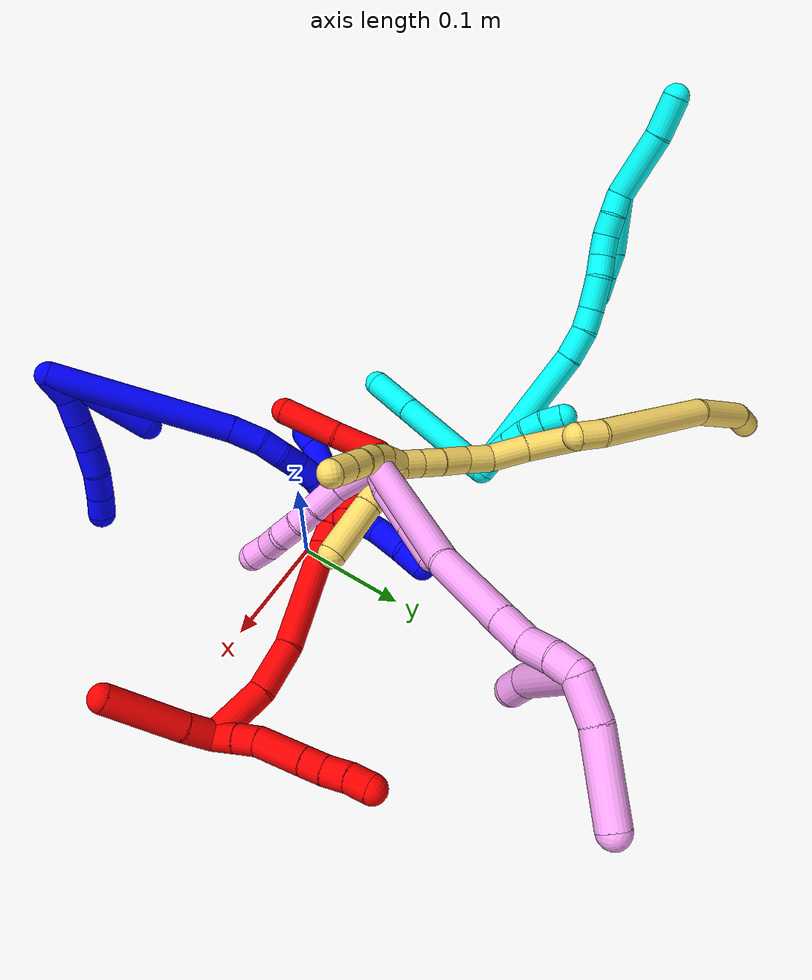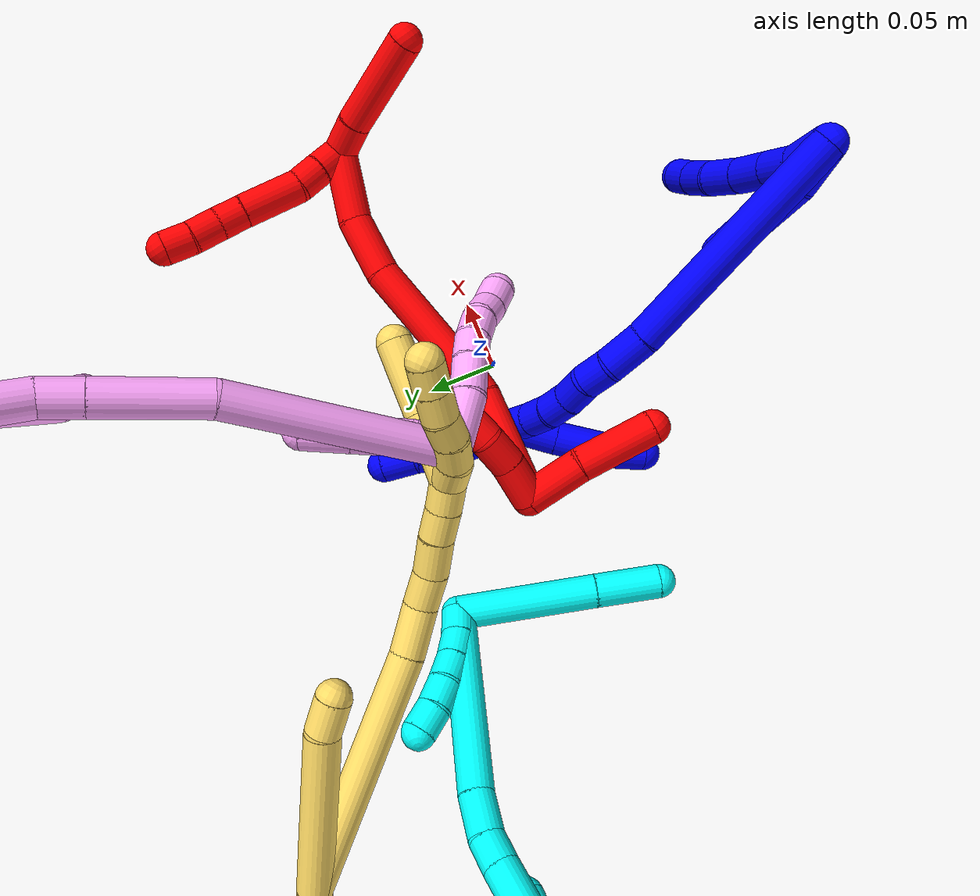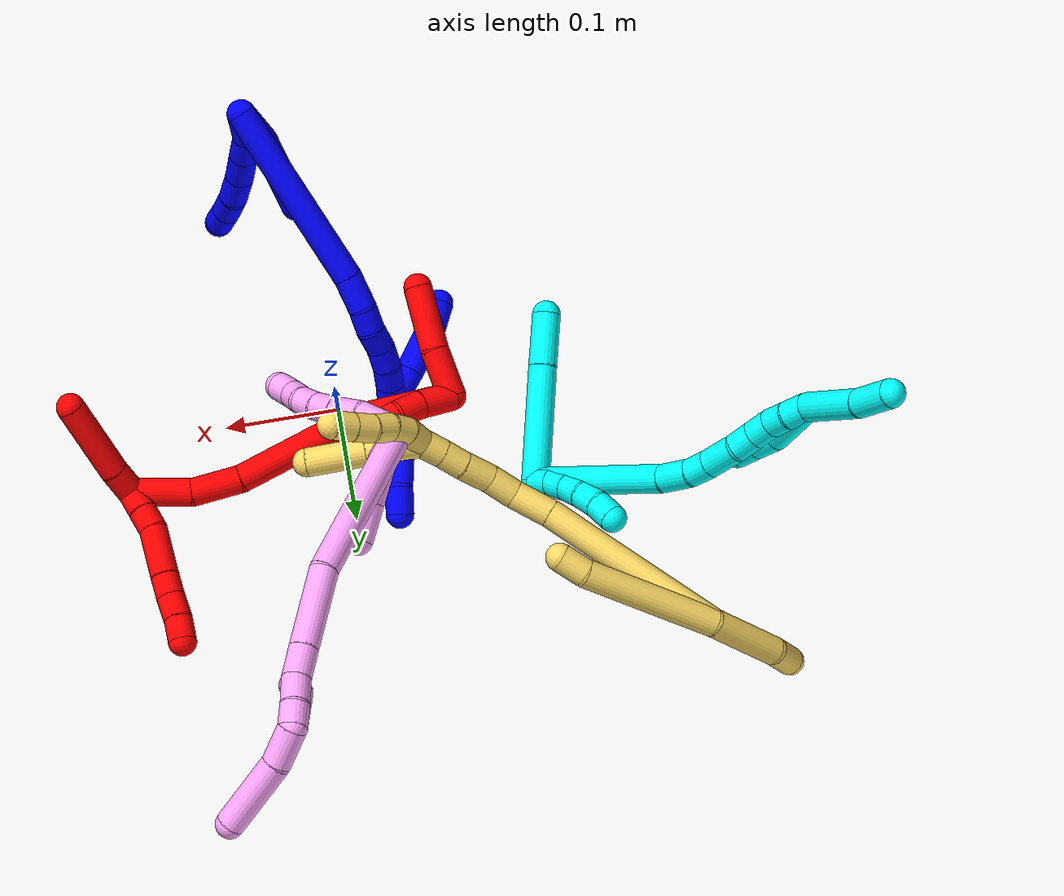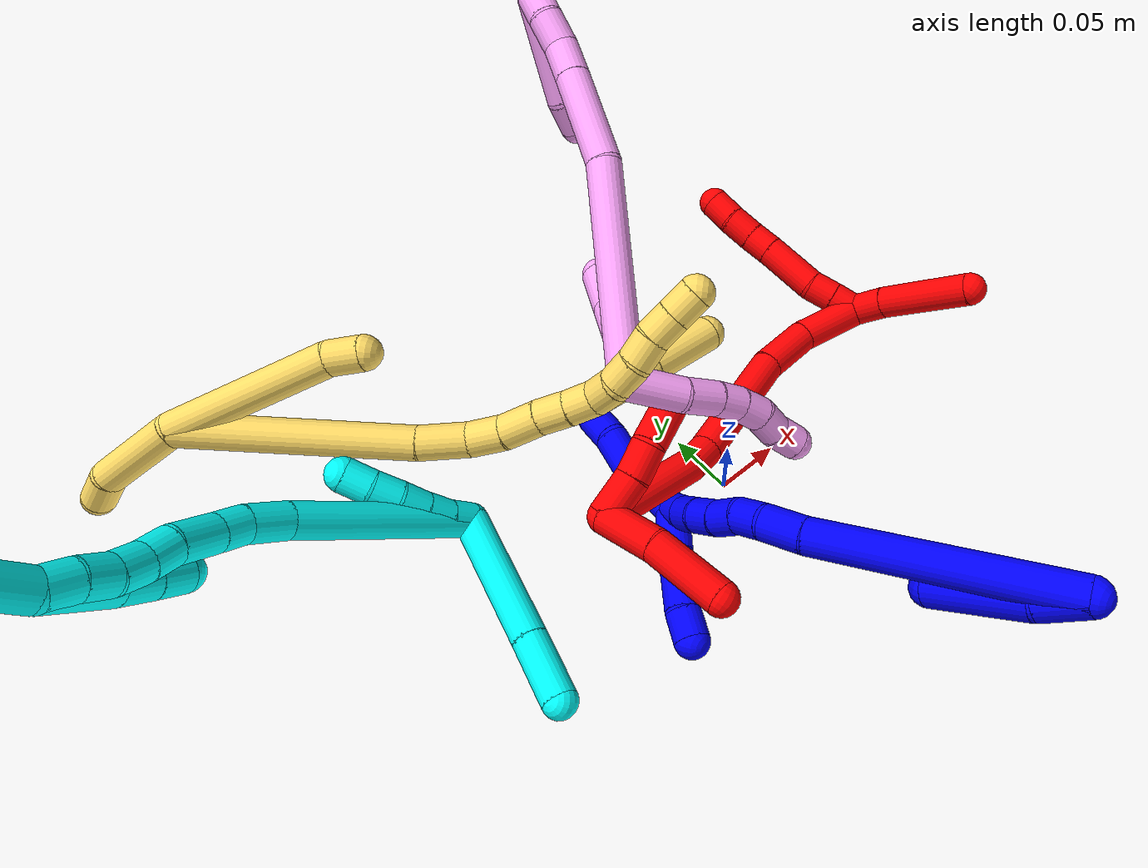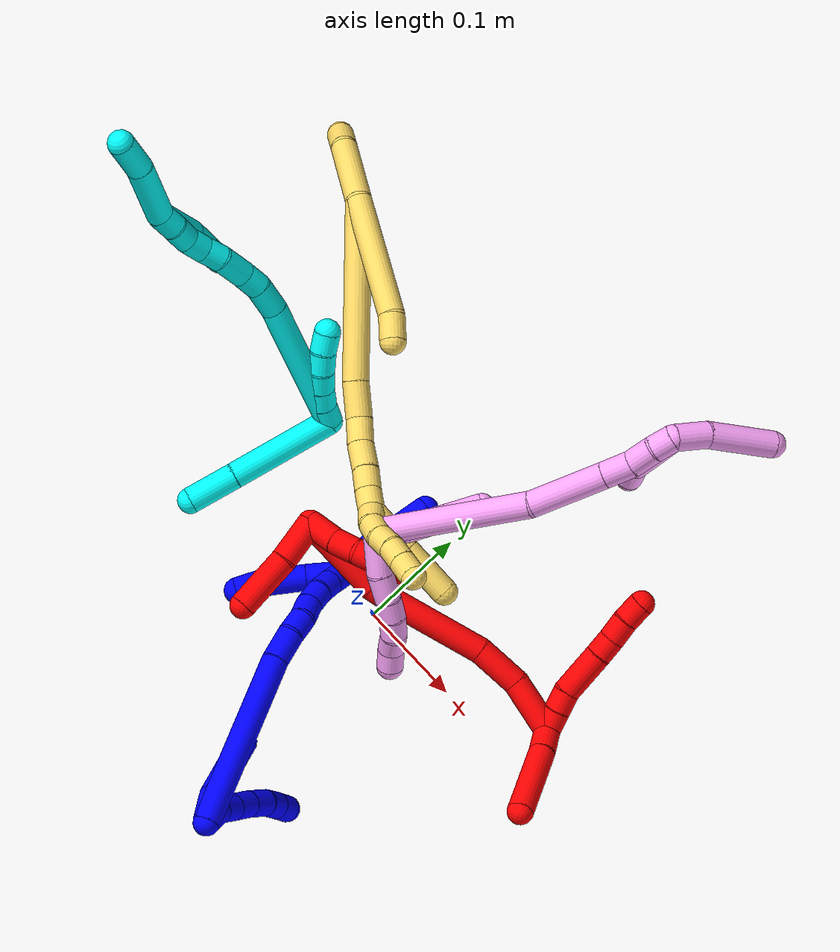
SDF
<sdf version="1.7">
 <world name="default">
  <plugin name="TubeGeneratorPlugin" filename="libtube_generator_plugin.so"/>
  <model name="photoneo_s_sensor">
   <static>1</static>
   <pose>0 0 2 1.57079 1.57079 3.14159</pose>
   <link name="link">
    <inertial><mass>0.1</mass></inertial>
    <sensor name="sensor" type="depth">
     <update_rate>30</update_rate>
     <camera>
      <horizontal_fov>1.22</horizontal_fov>
      <image><width>1920</width><height>1200</height><format>B8G8R8</format></image>
      <clip><near>0.1</near><far>4</far></clip>
      <depth_camera><output>points</output></depth_camera>
     </camera>
     <plugin name="camera_plugin" filename="libgazebo_ros_depth_camera.so">
      <baseline>0.2</baseline>
      <alwaysOn>1</alwaysOn>
      <updateRate>0.0</updateRate>
      <cameraName>camera_ir</cameraName>
      <imageTopicName>/camera/color/image_raw</imageTopicName>
      <cameraInfoTopicName>/camera/color/camera_info</cameraInfoTopicName>
      <depthImageTopicName>/camera/depth/image_raw</depthImageTopicName>
      <depthImageCameraInfoTopicName>/camera/depth/camera_info</depthImageCameraInfoTopicName>
      <pointCloudTopicName>/camera/depth/points</pointCloudTopicName>
      <frameName>fr_optical</frameName>
      <pointCloudCutoff>0.1</pointCloudCutoff>
      <pointCloudCutoffMax>2.0</pointCloudCutoffMax>
      <distortionK1>0</distortionK1>
      <distortionK2>0</distortionK2>
      <distortionK3>0</distortionK3>
      <distortionT1>0</distortionT1>
      <distortionT2>0</distortionT2>
      <CxPrime>0</CxPrime>
      <Cx>0</Cx>
      <Cy>0</Cy>
      <focalLength>0</focalLength>
      <hackBaseline>0</hackBaseline>
     </plugin>
    </sensor>
   </link>
  </model>
  <gravity>0 0 -9.8</gravity>
  <magnetic_field>6e-06 2.3e-05 -4.2e-05</magnetic_field>
  <atmosphere type="adiabatic"/>
  <physics name="default_physics" default="0" type="ode">
   <max_step_size>0.003</max_step_size>
   <real_time_factor>1</real_time_factor>
   <real_time_update_rate>1000</real_time_update_rate>
   <max_contacts>10000</max_contacts>
   <ode>
    <solver>
     <type>quick</type>
     <iters>100</iters>
     <sor>1.3</sor>
     <use_dynamic_moi_rescaling>0</use_dynamic_moi_rescaling>
    </solver>
    <constraints>
     <contact_max_correcting_vel>0</contact_max_correcting_vel>
     <contact_surface_layer>0.001</contact_surface_layer>
     <cfm>0</cfm>
     <erp>0.2</erp>
    </constraints>
   </ode>
  </physics>
  <scene><ambient>0.4 0.4 0.4 1</ambient><background>0.7 0.7 0.7 1</background><shadows>0</shadows></scene>
  <audio><device>default</device></audio>
  <spherical_coordinates>
   <surface_model>EARTH_WGS84</surface_model>
   <latitude_deg>0</latitude_deg>
   <longitude_deg>0</longitude_deg>
   <elevation>0</elevation>
   <heading_deg>0</heading_deg>
  </spherical_coordinates>
  <model name="bin">
   <static>1</static>
   <link name="bottom">
    <collision name="collision-bottom">
     <pose>0 0 -0.01 0 -0 0</pose>
     <geometry><box><size>0.8 0.6 0.02</size></box></geometry>
     <surface>
      <friction><ode><mu>100</mu><mu2>100</mu2></ode></friction>
      <contact><collide_bitmask>65535</collide_bitmask></contact>
     </surface>
    </collision>
   </link>
   <link name="west_wall">
    <collision name="collision-west_wall">
     <pose>-0.41 0 0.1 0 -0 0</pose>
     <geometry><box><size>0.02 0.6 0.2</size></box></geometry>
     <surface>
      <friction><ode><mu>100</mu><mu2>100</mu2></ode></friction>
      <contact><collide_bitmask>65535</collide_bitmask></contact>
     </surface>
    </collision>
   </link>
   <link name="east_wall">
    <collision name="collision-east_wall">
     <pose>0.41 0 0.1 0 -0 0</pose>
     <geometry><box><size>0.02 0.6 0.2</size></box></geometry>
     <surface>
      <friction><ode><mu>100</mu><mu2>100</mu2></ode></friction>
      <contact><collide_bitmask>65535</collide_bitmask></contact>
     </surface>
    </collision>
   </link>
   <link name="south_wall">
    <collision name="collision-south_wall">
     <pose>0 -0.31 0.1 0 -0 0</pose>
     <geometry><box><size>0.8 0.02 0.2</size></box></geometry>
     <surface>
      <friction><ode><mu>100</mu><mu2>100</mu2></ode></friction>
      <contact><collide_bitmask>65535</collide_bitmask></contact>
     </surface>
    </collision>
   </link>
   <link name="north_wall">
    <collision name="collision-north_wall">
     <pose>0 0.31 0.1 0 -0 0</pose>
     <geometry><box><size>0.8 0.02 0.2</size></box></geometry>
     <surface>
      <friction><ode><mu>100</mu><mu2>100</mu2></ode></friction>
      <contact><collide_bitmask>65535</collide_bitmask></contact>
     </surface>
    </collision>
   </link>
  </model>
  <model name="1">
   <static>0</static>
   <link name="1">
    <collision name="collision-cylinder-e_1_2_8">
     <pose>0.006401 -0.003817 -0.011486 2.82076 0.486462 1.98595</pose>
     <geometry><cylinder><radius>0.0125</radius><length>0.027385</length></cylinder></geometry>
     <surface>
      <friction><ode><mu>1.16</mu><mu2>1.16</mu2><slip1>0</slip1><slip2>0</slip2></ode></friction>
      <contact><ode><kp>1e+06</kp><kd>1</kd><max_vel>0</max_vel><min_depth>0.001</min_depth></ode></contact>
     </surface>
    </collision>
    <visual name="visual-cylinder-e_1_2_8">
     <pose>0.006401 -0.003817 -0.011486 2.82076 0.486462 1.98595</pose>
     <geometry><cylinder><radius>0.0125</radius><length>0.027385</length></cylinder></geometry>
     <material><ambient>0 0 1 1</ambient></material>
    </visual>
    <collision name="collision-cylinder-e_2_8_9">
     <pose>0.021626 -0.009128 -0.031157 2.96105 0.814789 2.72807</pose>
     <geometry><cylinder><radius>0.0125</radius><length>0.024253</length></cylinder></geometry>
     <surface>
      <friction><ode><mu>1.16</mu><mu2>1.16</mu2><slip1>0</slip1><slip2>0</slip2></ode></friction>
      <contact><ode><kp>1e+06</kp><kd>1</kd><max_vel>0</max_vel><min_depth>0.001</min_depth></ode></contact>
     </surface>
    </collision>
    <visual name="visual-cylinder-e_2_8_9">
     <pose>0.021626 -0.009128 -0.031157 2.96105 0.814789 2.72807</pose>
     <geometry><cylinder><radius>0.0125</radius><length>0.024253</length></cylinder></geometry>
     <material><ambient>0 0 1 1</ambient></material>
    </visual>
    <collision name="collision-cylinder-e_3_9_10">
     <pose>0.040015 -0.012068 -0.048737 2.9889 0.788498 2.77793</pose>
     <geometry><cylinder><radius>0.0125</radius><length>0.026974</length></cylinder></geometry>
     <surface>
      <friction><ode><mu>1.16</mu><mu2>1.16</mu2><slip1>0</slip1><slip2>0</slip2></ode></friction>
      <contact><ode><kp>1e+06</kp><kd>1</kd><max_vel>0</max_vel><min_depth>0.001</min_depth></ode></contact>
     </surface>
    </collision>
    <visual name="visual-cylinder-e_3_9_10">
     <pose>0.040015 -0.012068 -0.048737 2.9889 0.788498 2.77793</pose>
     <geometry><cylinder><radius>0.0125</radius><length>0.026974</length></cylinder></geometry>
     <material><ambient>0 0 1 1</ambient></material>
    </visual>
    <collision name="collision-cylinder-e_4_10_11">
     <pose>0.059469 -0.013922 -0.067099 3.09611 0.833801 3.03897</pose>
     <geometry><cylinder><radius>0.0125</radius><length>0.026707</length></cylinder></geometry>
     <surface>
      <friction><ode><mu>1.16</mu><mu2>1.16</mu2><slip1>0</slip1><slip2>0</slip2></ode></friction>
      <contact><ode><kp>1e+06</kp><kd>1</kd><max_vel>0</max_vel><min_depth>0.001</min_depth></ode></contact>
     </surface>
    </collision>
    <visual name="visual-cylinder-e_4_10_11">
     <pose>0.059469 -0.013922 -0.067099 3.09611 0.833801 3.03897</pose>
     <geometry><cylinder><radius>0.0125</radius><length>0.026707</length></cylinder></geometry>
     <material><ambient>0 0 1 1</ambient></material>
    </visual>
    <collision name="collision-cylinder-e_5_11_12">
     <pose>0.079686 -0.015956 -0.082257 2.88482 1.01583 2.6858</pose>
     <geometry><cylinder><radius>0.0125</radius><length>0.024305</length></cylinder></geometry>
     <surface>
      <friction><ode><mu>1.16</mu><mu2>1.16</mu2><slip1>0</slip1><slip2>0</slip2></ode></friction>
      <contact><ode><kp>1e+06</kp><kd>1</kd><max_vel>0</max_vel><min_depth>0.001</min_depth></ode></contact>
     </surface>
    </collision>
    <visual name="visual-cylinder-e_5_11_12">
     <pose>0.079686 -0.015956 -0.082257 2.88482 1.01583 2.6858</pose>
     <geometry><cylinder><radius>0.0125</radius><length>0.024305</length></cylinder></geometry>
     <material><ambient>0 0 1 1</ambient></material>
    </visual>
    <collision name="collision-cylinder-e_6_12_6">
     <pose>0.098894 -0.018218 -0.093406 3.01402 1.05827 2.92399</pose>
     <geometry><cylinder><radius>0.0125</radius><length>0.020375</length></cylinder></geometry>
     <surface>
      <friction><ode><mu>1.16</mu><mu2>1.16</mu2><slip1>0</slip1><slip2>0</slip2></ode></friction>
      <contact><ode><kp>1e+06</kp><kd>1</kd><max_vel>0</max_vel><min_depth>0.001</min_depth></ode></contact>
     </surface>
    </collision>
    <visual name="visual-cylinder-e_6_12_6">
     <pose>0.098894 -0.018218 -0.093406 3.01402 1.05827 2.92399</pose>
     <geometry><cylinder><radius>0.0125</radius><length>0.020375</length></cylinder></geometry>
     <material><ambient>0 0 1 1</ambient></material>
    </visual>
    <collision name="collision-cylinder-e_1_2_13">
     <pose>0.000329 -0.006938 -0.014336 2.69086 0.020668 0.090092</pose>
     <geometry><cylinder><radius>0.0125</radius><length>0.031861</length></cylinder></geometry>
     <surface>
      <friction><ode><mu>1.16</mu><mu2>1.16</mu2><slip1>0</slip1><slip2>0</slip2></ode></friction>
      <contact><ode><kp>1e+06</kp><kd>1</kd><max_vel>0</max_vel><min_depth>0.001</min_depth></ode></contact>
     </surface>
    </collision>
    <visual name="visual-cylinder-e_1_2_13">
     <pose>0.000329 -0.006938 -0.014336 2.69086 0.020668 0.090092</pose>
     <geometry><cylinder><radius>0.0125</radius><length>0.031861</length></cylinder></geometry>
     <material><ambient>0 0 1 1</ambient></material>
    </visual>
    <collision name="collision-cylinder-e_2_13_5">
     <pose>0.004341 -0.021953 -0.061566 2.90081 0.10831 0.842511</pose>
     <geometry><cylinder><radius>0.0125</radius><length>0.068139</length></cylinder></geometry>
     <surface>
      <friction><ode><mu>1.16</mu><mu2>1.16</mu2><slip1>0</slip1><slip2>0</slip2></ode></friction>
      <contact><ode><kp>1e+06</kp><kd>1</kd><max_vel>0</max_vel><min_depth>0.001</min_depth></ode></contact>
     </surface>
    </collision>
    <visual name="visual-cylinder-e_2_13_5">
     <pose>0.004341 -0.021953 -0.061566 2.90081 0.10831 0.842511</pose>
     <geometry><cylinder><radius>0.0125</radius><length>0.068139</length></cylinder></geometry>
     <material><ambient>0 0 1 1</ambient></material>
    </visual>
    <collision name="collision-cylinder-e_1_2_14">
     <pose>-0.01766 -0.013155 -0.081081 2.98074 -0.21177 -1.84396</pose>
     <geometry><cylinder><radius>0.0125</radius><length>0.168036</length></cylinder></geometry>
     <surface>
      <friction><ode><mu>1.16</mu><mu2>1.16</mu2><slip1>0</slip1><slip2>0</slip2></ode></friction>
      <contact><ode><kp>1e+06</kp><kd>1</kd><max_vel>0</max_vel><min_depth>0.001</min_depth></ode></contact>
     </surface>
    </collision>
    <visual name="visual-cylinder-e_1_2_14">
     <pose>-0.01766 -0.013155 -0.081081 2.98074 -0.21177 -1.84396</pose>
     <geometry><cylinder><radius>0.0125</radius><length>0.168036</length></cylinder></geometry>
     <material><ambient>0 0 1 1</ambient></material>
    </visual>
    <collision name="collision-cylinder-e_2_14_15">
     <pose>-0.037207 -0.027156 -0.177069 3.08499 -0.125726 -2.29638</pose>
     <geometry><cylinder><radius>0.0125</radius><length>0.0301</length></cylinder></geometry>
     <surface>
      <friction><ode><mu>1.16</mu><mu2>1.16</mu2><slip1>0</slip1><slip2>0</slip2></ode></friction>
      <contact><ode><kp>1e+06</kp><kd>1</kd><max_vel>0</max_vel><min_depth>0.001</min_depth></ode></contact>
     </surface>
    </collision>
    <visual name="visual-cylinder-e_2_14_15">
     <pose>-0.037207 -0.027156 -0.177069 3.08499 -0.125726 -2.29638</pose>
     <geometry><cylinder><radius>0.0125</radius><length>0.0301</length></cylinder></geometry>
     <material><ambient>0 0 1 1</ambient></material>
    </visual>
    <collision name="collision-cylinder-e_3_15_16">
     <pose>-0.038079 -0.029164 -0.202348 3.02982 0.096962 1.42888</pose>
     <geometry><cylinder><radius>0.0125</radius><length>0.020971</length></cylinder></geometry>
     <surface>
      <friction><ode><mu>1.16</mu><mu2>1.16</mu2><slip1>0</slip1><slip2>0</slip2></ode></friction>
      <contact><ode><kp>1e+06</kp><kd>1</kd><max_vel>0</max_vel><min_depth>0.001</min_depth></ode></contact>
     </surface>
    </collision>
    <visual name="visual-cylinder-e_3_15_16">
     <pose>-0.038079 -0.029164 -0.202348 3.02982 0.096962 1.42888</pose>
     <geometry><cylinder><radius>0.0125</radius><length>0.020971</length></cylinder></geometry>
     <material><ambient>0 0 1 1</ambient></material>
    </visual>
    <collision name="collision-cylinder-e_4_16_17">
     <pose>-0.034979 -0.034067 -0.2222 2.76599 0.201779 0.978916</pose>
     <geometry><cylinder><radius>0.0125</radius><length>0.020804</length></cylinder></geometry>
     <surface>
      <friction><ode><mu>1.16</mu><mu2>1.16</mu2><slip1>0</slip1><slip2>0</slip2></ode></friction>
      <contact><ode><kp>1e+06</kp><kd>1</kd><max_vel>0</max_vel><min_depth>0.001</min_depth></ode></contact>
     </surface>
    </collision>
    <visual name="visual-cylinder-e_4_16_17">
     <pose>-0.034979 -0.034067 -0.2222 2.76599 0.201779 0.978916</pose>
     <geometry><cylinder><radius>0.0125</radius><length>0.020804</length></cylinder></geometry>
     <material><ambient>0 0 1 1</ambient></material>
    </visual>
    <collision name="collision-cylinder-e_5_17_18">
     <pose>-0.030638 -0.039689 -0.24126 2.94743 0.227166 1.72827</pose>
     <geometry><cylinder><radius>0.0125</radius><length>0.02004</length></cylinder></geometry>
     <surface>
      <friction><ode><mu>1.16</mu><mu2>1.16</mu2><slip1>0</slip1><slip2>0</slip2></ode></friction>
      <contact><ode><kp>1e+06</kp><kd>1</kd><max_vel>0</max_vel><min_depth>0.001</min_depth></ode></contact>
     </surface>
    </collision>
    <visual name="visual-cylinder-e_5_17_18">
     <pose>-0.030638 -0.039689 -0.24126 2.94743 0.227166 1.72827</pose>
     <geometry><cylinder><radius>0.0125</radius><length>0.02004</length></cylinder></geometry>
     <material><ambient>0 0 1 1</ambient></material>
    </visual>
    <collision name="collision-cylinder-e_6_18_19">
     <pose>-0.024282 -0.043114 -0.259847 2.97209 0.421593 2.38571</pose>
     <geometry><cylinder><radius>0.0125</radius><length>0.020031</length></cylinder></geometry>
     <surface>
      <friction><ode><mu>1.16</mu><mu2>1.16</mu2><slip1>0</slip1><slip2>0</slip2></ode></friction>
      <contact><ode><kp>1e+06</kp><kd>1</kd><max_vel>0</max_vel><min_depth>0.001</min_depth></ode></contact>
     </surface>
    </collision>
    <visual name="visual-cylinder-e_6_18_19">
     <pose>-0.024282 -0.043114 -0.259847 2.97209 0.421593 2.38571</pose>
     <geometry><cylinder><radius>0.0125</radius><length>0.020031</length></cylinder></geometry>
     <material><ambient>0 0 1 1</ambient></material>
    </visual>
    <collision name="collision-cylinder-e_7_19_1">
     <pose>-0.015992 -0.045414 -0.27791 3.05804 0.43222 2.76532</pose>
     <geometry><cylinder><radius>0.0125</radius><length>0.020016</length></cylinder></geometry>
     <surface>
      <friction><ode><mu>1.16</mu><mu2>1.16</mu2><slip1>0</slip1><slip2>0</slip2></ode></friction>
      <contact><ode><kp>1e+06</kp><kd>1</kd><max_vel>0</max_vel><min_depth>0.001</min_depth></ode></contact>
     </surface>
    </collision>
    <visual name="visual-cylinder-e_7_19_1">
     <pose>-0.015992 -0.045414 -0.27791 3.05804 0.43222 2.76532</pose>
     <geometry><cylinder><radius>0.0125</radius><length>0.020016</length></cylinder></geometry>
     <material><ambient>0 0 1 1</ambient></material>
    </visual>
    <collision name="collision-cylinder-e_1_1_20">
     <pose>-0.014886 -0.059277 -0.276838 0.912817 -0.184281 -0.090674</pose>
     <geometry><cylinder><radius>0.0125</radius><length>0.033695</length></cylinder></geometry>
     <surface>
      <friction><ode><mu>1.16</mu><mu2>1.16</mu2><slip1>0</slip1><slip2>0</slip2></ode></friction>
      <contact><ode><kp>1e+06</kp><kd>1</kd><max_vel>0</max_vel><min_depth>0.001</min_depth></ode></contact>
     </surface>
    </collision>
    <visual name="visual-cylinder-e_1_1_20">
     <pose>-0.014886 -0.059277 -0.276838 0.912817 -0.184281 -0.090674</pose>
     <geometry><cylinder><radius>0.0125</radius><length>0.033695</length></cylinder></geometry>
     <material><ambient>0 0 1 1</ambient></material>
    </visual>
    <collision name="collision-cylinder-e_2_20_21">
     <pose>-0.022323 -0.088946 -0.251975 0.843772 -0.193711 -0.087162</pose>
     <geometry><cylinder><radius>0.0125</radius><length>0.045186</length></cylinder></geometry>
     <surface>
      <friction><ode><mu>1.16</mu><mu2>1.16</mu2><slip1>0</slip1><slip2>0</slip2></ode></friction>
      <contact><ode><kp>1e+06</kp><kd>1</kd><max_vel>0</max_vel><min_depth>0.001</min_depth></ode></contact>
     </surface>
    </collision>
    <visual name="visual-cylinder-e_2_20_21">
     <pose>-0.022323 -0.088946 -0.251975 0.843772 -0.193711 -0.087162</pose>
     <geometry><cylinder><radius>0.0125</radius><length>0.045186</length></cylinder></geometry>
     <material><ambient>0 0 1 1</ambient></material>
    </visual>
    <collision name="collision-cylinder-e_3_21_4">
     <pose>-0.026817 -0.112854 -0.229652 0.768985 -0.013729 -0.005555</pose>
     <geometry><cylinder><radius>0.0125</radius><length>0.021119</length></cylinder></geometry>
     <surface>
      <friction><ode><mu>1.16</mu><mu2>1.16</mu2><slip1>0</slip1><slip2>0</slip2></ode></friction>
      <contact><ode><kp>1e+06</kp><kd>1</kd><max_vel>0</max_vel><min_depth>0.001</min_depth></ode></contact>
     </surface>
    </collision>
    <visual name="visual-cylinder-e_3_21_4">
     <pose>-0.026817 -0.112854 -0.229652 0.768985 -0.013729 -0.005555</pose>
     <geometry><cylinder><radius>0.0125</radius><length>0.021119</length></cylinder></geometry>
     <material><ambient>0 0 1 1</ambient></material>
    </visual>
    <collision name="collision-cylinder-e_1_1_22">
     <pose>-0.016473 -0.038896 -0.306718 -2.78863 -0.218502 1.10283</pose>
     <geometry><cylinder><radius>0.0125</radius><length>0.043123</length></cylinder></geometry>
     <surface>
      <friction><ode><mu>1.16</mu><mu2>1.16</mu2><slip1>0</slip1><slip2>0</slip2></ode></friction>
      <contact><ode><kp>1e+06</kp><kd>1</kd><max_vel>0</max_vel><min_depth>0.001</min_depth></ode></contact>
     </surface>
    </collision>
    <visual name="visual-cylinder-e_1_1_22">
     <pose>-0.016473 -0.038896 -0.306718 -2.78863 -0.218502 1.10283</pose>
     <geometry><cylinder><radius>0.0125</radius><length>0.043123</length></cylinder></geometry>
     <material><ambient>0 0 1 1</ambient></material>
    </visual>
    <collision name="collision-cylinder-e_2_22_23">
     <pose>-0.023806 -0.022644 -0.33958 -2.54125 -0.16584 0.524648</pose>
     <geometry><cylinder><radius>0.0125</radius><length>0.032222</length></cylinder></geometry>
     <surface>
      <friction><ode><mu>1.16</mu><mu2>1.16</mu2><slip1>0</slip1><slip2>0</slip2></ode></friction>
      <contact><ode><kp>1e+06</kp><kd>1</kd><max_vel>0</max_vel><min_depth>0.001</min_depth></ode></contact>
     </surface>
    </collision>
    <visual name="visual-cylinder-e_2_22_23">
     <pose>-0.023806 -0.022644 -0.33958 -2.54125 -0.16584 0.524648</pose>
     <geometry><cylinder><radius>0.0125</radius><length>0.032222</length></cylinder></geometry>
     <material><ambient>0 0 1 1</ambient></material>
    </visual>
    <collision name="collision-cylinder-e_3_23_3">
     <pose>-0.026404 -0.009375 -0.364248 -2.786 0.004996 -0.027804</pose>
     <geometry><cylinder><radius>0.0125</radius><length>0.024655</length></cylinder></geometry>
     <surface>
      <friction><ode><mu>1.16</mu><mu2>1.16</mu2><slip1>0</slip1><slip2>0</slip2></ode></friction>
      <contact><ode><kp>1e+06</kp><kd>1</kd><max_vel>0</max_vel><min_depth>0.001</min_depth></ode></contact>
     </surface>
    </collision>
    <visual name="visual-cylinder-e_3_23_3">
     <pose>-0.026404 -0.009375 -0.364248 -2.786 0.004996 -0.027804</pose>
     <geometry><cylinder><radius>0.0125</radius><length>0.024655</length></cylinder></geometry>
     <material><ambient>0 0 1 1</ambient></material>
    </visual>
    <collision name="collision-sphere-3">
     <pose>-0.026343 -0.005084 -0.375804 0 -0 0</pose>
     <geometry><sphere><radius>0.0125</radius></sphere></geometry>
     <surface>
      <friction><ode><mu>1.16</mu><mu2>1.16</mu2><slip1>0</slip1><slip2>0</slip2></ode></friction>
      <contact><ode><kp>1e+06</kp><kd>1</kd><max_vel>0</max_vel><min_depth>0.001</min_depth></ode></contact>
     </surface>
    </collision>
    <visual name="visual-sphere-3">
     <pose>-0.026343 -0.005084 -0.375804 0 -0 0</pose>
     <geometry><sphere><radius>0.0125</radius></sphere></geometry>
     <material><ambient>0 0 1 1</ambient></material>
    </visual>
    <collision name="collision-sphere-23">
     <pose>-0.026466 -0.013667 -0.352692 0 -0 0</pose>
     <geometry><sphere><radius>0.0125</radius></sphere></geometry>
     <surface>
      <friction><ode><mu>1.16</mu><mu2>1.16</mu2><slip1>0</slip1><slip2>0</slip2></ode></friction>
      <contact><ode><kp>1e+06</kp><kd>1</kd><max_vel>0</max_vel><min_depth>0.001</min_depth></ode></contact>
     </surface>
    </collision>
    <visual name="visual-sphere-23">
     <pose>-0.026466 -0.013667 -0.352692 0 -0 0</pose>
     <geometry><sphere><radius>0.0125</radius></sphere></geometry>
     <material><ambient>0 0 1 1</ambient></material>
    </visual>
    <collision name="collision-sphere-22">
     <pose>-0.021147 -0.03162 -0.326469 0 -0 0</pose>
     <geometry><sphere><radius>0.0125</radius></sphere></geometry>
     <surface>
      <friction><ode><mu>1.16</mu><mu2>1.16</mu2><slip1>0</slip1><slip2>0</slip2></ode></friction>
      <contact><ode><kp>1e+06</kp><kd>1</kd><max_vel>0</max_vel><min_depth>0.001</min_depth></ode></contact>
     </surface>
    </collision>
    <visual name="visual-sphere-22">
     <pose>-0.021147 -0.03162 -0.326469 0 -0 0</pose>
     <geometry><sphere><radius>0.0125</radius></sphere></geometry>
     <material><ambient>0 0 1 1</ambient></material>
    </visual>
    <collision name="collision-sphere-4">
     <pose>-0.026962 -0.120196 -0.222064 0 -0 0</pose>
     <geometry><sphere><radius>0.0125</radius></sphere></geometry>
     <surface>
      <friction><ode><mu>1.16</mu><mu2>1.16</mu2><slip1>0</slip1><slip2>0</slip2></ode></friction>
      <contact><ode><kp>1e+06</kp><kd>1</kd><max_vel>0</max_vel><min_depth>0.001</min_depth></ode></contact>
     </surface>
    </collision>
    <visual name="visual-sphere-4">
     <pose>-0.026962 -0.120196 -0.222064 0 -0 0</pose>
     <geometry><sphere><radius>0.0125</radius></sphere></geometry>
     <material><ambient>0 0 1 1</ambient></material>
    </visual>
    <collision name="collision-sphere-21">
     <pose>-0.026672 -0.105511 -0.237239 0 -0 0</pose>
     <geometry><sphere><radius>0.0125</radius></sphere></geometry>
     <surface>
      <friction><ode><mu>1.16</mu><mu2>1.16</mu2><slip1>0</slip1><slip2>0</slip2></ode></friction>
      <contact><ode><kp>1e+06</kp><kd>1</kd><max_vel>0</max_vel><min_depth>0.001</min_depth></ode></contact>
     </surface>
    </collision>
    <visual name="visual-sphere-21">
     <pose>-0.026672 -0.105511 -0.237239 0 -0 0</pose>
     <geometry><sphere><radius>0.0125</radius></sphere></geometry>
     <material><ambient>0 0 1 1</ambient></material>
    </visual>
    <collision name="collision-sphere-20">
     <pose>-0.017974 -0.072382 -0.26671 0 -0 0</pose>
     <geometry><sphere><radius>0.0125</radius></sphere></geometry>
     <surface>
      <friction><ode><mu>1.16</mu><mu2>1.16</mu2><slip1>0</slip1><slip2>0</slip2></ode></friction>
      <contact><ode><kp>1e+06</kp><kd>1</kd><max_vel>0</max_vel><min_depth>0.001</min_depth></ode></contact>
     </surface>
    </collision>
    <visual name="visual-sphere-20">
     <pose>-0.017974 -0.072382 -0.26671 0 -0 0</pose>
     <geometry><sphere><radius>0.0125</radius></sphere></geometry>
     <material><ambient>0 0 1 1</ambient></material>
    </visual>
    <collision name="collision-sphere-12">
     <pose>0.090015 -0.017582 -0.088451 0 -0 0</pose>
     <geometry><sphere><radius>0.0125</radius></sphere></geometry>
     <surface>
      <friction><ode><mu>1.16</mu><mu2>1.16</mu2><slip1>0</slip1><slip2>0</slip2></ode></friction>
      <contact><ode><kp>1e+06</kp><kd>1</kd><max_vel>0</max_vel><min_depth>0.001</min_depth></ode></contact>
     </surface>
    </collision>
    <visual name="visual-sphere-12">
     <pose>0.090015 -0.017582 -0.088451 0 -0 0</pose>
     <geometry><sphere><radius>0.0125</radius></sphere></geometry>
     <material><ambient>0 0 1 1</ambient></material>
    </visual>
    <collision name="collision-sphere-11">
     <pose>0.069358 -0.01433 -0.076064 0 -0 0</pose>
     <geometry><sphere><radius>0.0125</radius></sphere></geometry>
     <surface>
      <friction><ode><mu>1.16</mu><mu2>1.16</mu2><slip1>0</slip1><slip2>0</slip2></ode></friction>
      <contact><ode><kp>1e+06</kp><kd>1</kd><max_vel>0</max_vel><min_depth>0.001</min_depth></ode></contact>
     </surface>
    </collision>
    <visual name="visual-sphere-11">
     <pose>0.069358 -0.01433 -0.076064 0 -0 0</pose>
     <geometry><sphere><radius>0.0125</radius></sphere></geometry>
     <material><ambient>0 0 1 1</ambient></material>
    </visual>
    <collision name="collision-sphere-10">
     <pose>0.049581 -0.013514 -0.058134 0 -0 0</pose>
     <geometry><sphere><radius>0.0125</radius></sphere></geometry>
     <surface>
      <friction><ode><mu>1.16</mu><mu2>1.16</mu2><slip1>0</slip1><slip2>0</slip2></ode></friction>
      <contact><ode><kp>1e+06</kp><kd>1</kd><max_vel>0</max_vel><min_depth>0.001</min_depth></ode></contact>
     </surface>
    </collision>
    <visual name="visual-sphere-10">
     <pose>0.049581 -0.013514 -0.058134 0 -0 0</pose>
     <geometry><sphere><radius>0.0125</radius></sphere></geometry>
     <material><ambient>0 0 1 1</ambient></material>
    </visual>
    <collision name="collision-sphere-9">
     <pose>0.030449 -0.010622 -0.039341 0 -0 0</pose>
     <geometry><sphere><radius>0.0125</radius></sphere></geometry>
     <surface>
      <friction><ode><mu>1.16</mu><mu2>1.16</mu2><slip1>0</slip1><slip2>0</slip2></ode></friction>
      <contact><ode><kp>1e+06</kp><kd>1</kd><max_vel>0</max_vel><min_depth>0.001</min_depth></ode></contact>
     </surface>
    </collision>
    <visual name="visual-sphere-9">
     <pose>0.030449 -0.010622 -0.039341 0 -0 0</pose>
     <geometry><sphere><radius>0.0125</radius></sphere></geometry>
     <material><ambient>0 0 1 1</ambient></material>
    </visual>
    <collision name="collision-sphere-2">
     <geometry><sphere><radius>0.0125</radius></sphere></geometry>
     <surface>
      <friction><ode><mu>1.16</mu><mu2>1.16</mu2><slip1>0</slip1><slip2>0</slip2></ode></friction>
      <contact><ode><kp>1e+06</kp><kd>1</kd><max_vel>0</max_vel><min_depth>0.001</min_depth></ode></contact>
     </surface>
    </collision>
    <visual name="visual-sphere-2">
     <geometry><sphere><radius>0.0125</radius></sphere></geometry>
     <material><ambient>0 0 1 1</ambient></material>
    </visual>
    <collision name="collision-sphere-19">
     <pose>-0.020184 -0.044656 -0.268854 0 -0 0</pose>
     <geometry><sphere><radius>0.0125</radius></sphere></geometry>
     <surface>
      <friction><ode><mu>1.16</mu><mu2>1.16</mu2><slip1>0</slip1><slip2>0</slip2></ode></friction>
      <contact><ode><kp>1e+06</kp><kd>1</kd><max_vel>0</max_vel><min_depth>0.001</min_depth></ode></contact>
     </surface>
    </collision>
    <visual name="visual-sphere-19">
     <pose>-0.020184 -0.044656 -0.268854 0 -0 0</pose>
     <geometry><sphere><radius>0.0125</radius></sphere></geometry>
     <material><ambient>0 0 1 1</ambient></material>
    </visual>
    <collision name="collision-sphere-8">
     <pose>0.012802 -0.007634 -0.022973 0 -0 0</pose>
     <geometry><sphere><radius>0.0125</radius></sphere></geometry>
     <surface>
      <friction><ode><mu>1.16</mu><mu2>1.16</mu2><slip1>0</slip1><slip2>0</slip2></ode></friction>
      <contact><ode><kp>1e+06</kp><kd>1</kd><max_vel>0</max_vel><min_depth>0.001</min_depth></ode></contact>
     </surface>
    </collision>
    <visual name="visual-sphere-8">
     <pose>0.012802 -0.007634 -0.022973 0 -0 0</pose>
     <geometry><sphere><radius>0.0125</radius></sphere></geometry>
     <material><ambient>0 0 1 1</ambient></material>
    </visual>
    <collision name="collision-sphere-6">
     <pose>0.107773 -0.018853 -0.098361 0 -0 0</pose>
     <geometry><sphere><radius>0.0125</radius></sphere></geometry>
     <surface>
      <friction><ode><mu>1.16</mu><mu2>1.16</mu2><slip1>0</slip1><slip2>0</slip2></ode></friction>
      <contact><ode><kp>1e+06</kp><kd>1</kd><max_vel>0</max_vel><min_depth>0.001</min_depth></ode></contact>
     </surface>
    </collision>
    <visual name="visual-sphere-6">
     <pose>0.107773 -0.018853 -0.098361 0 -0 0</pose>
     <geometry><sphere><radius>0.0125</radius></sphere></geometry>
     <material><ambient>0 0 1 1</ambient></material>
    </visual>
    <collision name="collision-sphere-13">
     <pose>0.000658 -0.013877 -0.028673 0 -0 0</pose>
     <geometry><sphere><radius>0.0125</radius></sphere></geometry>
     <surface>
      <friction><ode><mu>1.16</mu><mu2>1.16</mu2><slip1>0</slip1><slip2>0</slip2></ode></friction>
      <contact><ode><kp>1e+06</kp><kd>1</kd><max_vel>0</max_vel><min_depth>0.001</min_depth></ode></contact>
     </surface>
    </collision>
    <visual name="visual-sphere-13">
     <pose>0.000658 -0.013877 -0.028673 0 -0 0</pose>
     <geometry><sphere><radius>0.0125</radius></sphere></geometry>
     <material><ambient>0 0 1 1</ambient></material>
    </visual>
    <collision name="collision-sphere-5">
     <pose>0.008024 -0.03003 -0.094458 0 -0 0</pose>
     <geometry><sphere><radius>0.0125</radius></sphere></geometry>
     <surface>
      <friction><ode><mu>1.16</mu><mu2>1.16</mu2><slip1>0</slip1><slip2>0</slip2></ode></friction>
      <contact><ode><kp>1e+06</kp><kd>1</kd><max_vel>0</max_vel><min_depth>0.001</min_depth></ode></contact>
     </surface>
    </collision>
    <visual name="visual-sphere-5">
     <pose>0.008024 -0.03003 -0.094458 0 -0 0</pose>
     <geometry><sphere><radius>0.0125</radius></sphere></geometry>
     <material><ambient>0 0 1 1</ambient></material>
    </visual>
    <collision name="collision-sphere-14">
     <pose>-0.03532 -0.026311 -0.162162 0 -0 0</pose>
     <geometry><sphere><radius>0.0125</radius></sphere></geometry>
     <surface>
      <friction><ode><mu>1.16</mu><mu2>1.16</mu2><slip1>0</slip1><slip2>0</slip2></ode></friction>
      <contact><ode><kp>1e+06</kp><kd>1</kd><max_vel>0</max_vel><min_depth>0.001</min_depth></ode></contact>
     </surface>
    </collision>
    <visual name="visual-sphere-14">
     <pose>-0.03532 -0.026311 -0.162162 0 -0 0</pose>
     <geometry><sphere><radius>0.0125</radius></sphere></geometry>
     <material><ambient>0 0 1 1</ambient></material>
    </visual>
    <collision name="collision-sphere-15">
     <pose>-0.039094 -0.028 -0.191977 0 -0 0</pose>
     <geometry><sphere><radius>0.0125</radius></sphere></geometry>
     <surface>
      <friction><ode><mu>1.16</mu><mu2>1.16</mu2><slip1>0</slip1><slip2>0</slip2></ode></friction>
      <contact><ode><kp>1e+06</kp><kd>1</kd><max_vel>0</max_vel><min_depth>0.001</min_depth></ode></contact>
     </surface>
    </collision>
    <visual name="visual-sphere-15">
     <pose>-0.039094 -0.028 -0.191977 0 -0 0</pose>
     <geometry><sphere><radius>0.0125</radius></sphere></geometry>
     <material><ambient>0 0 1 1</ambient></material>
    </visual>
    <collision name="collision-sphere-16">
     <pose>-0.037064 -0.030328 -0.212719 0 -0 0</pose>
     <geometry><sphere><radius>0.0125</radius></sphere></geometry>
     <surface>
      <friction><ode><mu>1.16</mu><mu2>1.16</mu2><slip1>0</slip1><slip2>0</slip2></ode></friction>
      <contact><ode><kp>1e+06</kp><kd>1</kd><max_vel>0</max_vel><min_depth>0.001</min_depth></ode></contact>
     </surface>
    </collision>
    <visual name="visual-sphere-16">
     <pose>-0.037064 -0.030328 -0.212719 0 -0 0</pose>
     <geometry><sphere><radius>0.0125</radius></sphere></geometry>
     <material><ambient>0 0 1 1</ambient></material>
    </visual>
    <collision name="collision-sphere-17">
     <pose>-0.032894 -0.037805 -0.231681 0 -0 0</pose>
     <geometry><sphere><radius>0.0125</radius></sphere></geometry>
     <surface>
      <friction><ode><mu>1.16</mu><mu2>1.16</mu2><slip1>0</slip1><slip2>0</slip2></ode></friction>
      <contact><ode><kp>1e+06</kp><kd>1</kd><max_vel>0</max_vel><min_depth>0.001</min_depth></ode></contact>
     </surface>
    </collision>
    <visual name="visual-sphere-17">
     <pose>-0.032894 -0.037805 -0.231681 0 -0 0</pose>
     <geometry><sphere><radius>0.0125</radius></sphere></geometry>
     <material><ambient>0 0 1 1</ambient></material>
    </visual>
    <collision name="collision-sphere-18">
     <pose>-0.028381 -0.041573 -0.250839 0 -0 0</pose>
     <geometry><sphere><radius>0.0125</radius></sphere></geometry>
     <surface>
      <friction><ode><mu>1.16</mu><mu2>1.16</mu2><slip1>0</slip1><slip2>0</slip2></ode></friction>
      <contact><ode><kp>1e+06</kp><kd>1</kd><max_vel>0</max_vel><min_depth>0.001</min_depth></ode></contact>
     </surface>
    </collision>
    <visual name="visual-sphere-18">
     <pose>-0.028381 -0.041573 -0.250839 0 -0 0</pose>
     <geometry><sphere><radius>0.0125</radius></sphere></geometry>
     <material><ambient>0 0 1 1</ambient></material>
    </visual>
    <collision name="collision-sphere-1">
     <pose>-0.011799 -0.046173 -0.286967 0 -0 0</pose>
     <geometry><sphere><radius>0.0125</radius></sphere></geometry>
     <surface>
      <friction><ode><mu>1.16</mu><mu2>1.16</mu2><slip1>0</slip1><slip2>0</slip2></ode></friction>
      <contact><ode><kp>1e+06</kp><kd>1</kd><max_vel>0</max_vel><min_depth>0.001</min_depth></ode></contact>
     </surface>
    </collision>
    <visual name="visual-sphere-1">
     <pose>-0.011799 -0.046173 -0.286967 0 -0 0</pose>
     <geometry><sphere><radius>0.0125</radius></sphere></geometry>
     <material><ambient>0 0 1 1</ambient></material>
    </visual>
    <inertial>
     <pose>-0.004818 -0.028605 -0.153156 0 -0 0</pose>
     <mass>0.75</mass>
     <inertia>
      <ixx>-0.000405</ixx>
      <ixy>0</ixy>
      <ixz>0</ixz>
      <iyy>-0.000234</iyy>
      <iyz>0</iyz>
      <izz>0.000116</izz>
     </inertia>
    </inertial>
   </link>
   <pose>0.039969 -0.241547 0.141198 0.932881 0.855567 -0.341959</pose>
  </model>
  <model name="2">
   <static>0</static>
   <link name="2">
    <collision name="collision-cylinder-e_1_2_8">
     <pose>-0.009237 0.005247 -0.000314 -1.63048 -1.05344 1.10609</pose>
     <geometry><cylinder><radius>0.0125</radius><length>0.021256</length></cylinder></geometry>
     <surface>
      <friction><ode><mu>1.16</mu><mu2>1.16</mu2><slip1>0</slip1><slip2>0</slip2></ode></friction>
      <contact><ode><kp>1e+06</kp><kd>1</kd><max_vel>0</max_vel><min_depth>0.001</min_depth></ode></contact>
     </surface>
    </collision>
    <visual name="visual-cylinder-e_1_2_8">
     <pose>-0.009237 0.005247 -0.000314 -1.63048 -1.05344 1.10609</pose>
     <geometry><cylinder><radius>0.0125</radius><length>0.021256</length></cylinder></geometry>
     <material><ambient>1 0 0 1</ambient></material>
    </visual>
    <collision name="collision-cylinder-e_2_8_9">
     <pose>-0.026948 0.015801 -0.001089 -1.65768 -1.00963 1.08494</pose>
     <geometry><cylinder><radius>0.0125</radius><length>0.020019</length></cylinder></geometry>
     <surface>
      <friction><ode><mu>1.16</mu><mu2>1.16</mu2><slip1>0</slip1><slip2>0</slip2></ode></friction>
      <contact><ode><kp>1e+06</kp><kd>1</kd><max_vel>0</max_vel><min_depth>0.001</min_depth></ode></contact>
     </surface>
    </collision>
    <visual name="visual-cylinder-e_2_8_9">
     <pose>-0.026948 0.015801 -0.001089 -1.65768 -1.00963 1.08494</pose>
     <geometry><cylinder><radius>0.0125</radius><length>0.020019</length></cylinder></geometry>
     <material><ambient>1 0 0 1</ambient></material>
    </visual>
    <collision name="collision-cylinder-e_3_9_10">
     <pose>-0.053018 0.034502 0.002703 -1.26322 -0.896848 0.676868</pose>
     <geometry><cylinder><radius>0.0125</radius><length>0.045038</length></cylinder></geometry>
     <surface>
      <friction><ode><mu>1.16</mu><mu2>1.16</mu2><slip1>0</slip1><slip2>0</slip2></ode></friction>
      <contact><ode><kp>1e+06</kp><kd>1</kd><max_vel>0</max_vel><min_depth>0.001</min_depth></ode></contact>
     </surface>
    </collision>
    <visual name="visual-cylinder-e_3_9_10">
     <pose>-0.053018 0.034502 0.002703 -1.26322 -0.896848 0.676868</pose>
     <geometry><cylinder><radius>0.0125</radius><length>0.045038</length></cylinder></geometry>
     <material><ambient>1 0 0 1</ambient></material>
    </visual>
    <collision name="collision-cylinder-e_4_10_11">
     <pose>-0.078279 0.054155 0.008497 -1.3296 -0.871588 0.699929</pose>
     <geometry><cylinder><radius>0.0125</radius><length>0.02003</length></cylinder></geometry>
     <surface>
      <friction><ode><mu>1.16</mu><mu2>1.16</mu2><slip1>0</slip1><slip2>0</slip2></ode></friction>
      <contact><ode><kp>1e+06</kp><kd>1</kd><max_vel>0</max_vel><min_depth>0.001</min_depth></ode></contact>
     </surface>
    </collision>
    <visual name="visual-cylinder-e_4_10_11">
     <pose>-0.078279 0.054155 0.008497 -1.3296 -0.871588 0.699929</pose>
     <geometry><cylinder><radius>0.0125</radius><length>0.02003</length></cylinder></geometry>
     <material><ambient>1 0 0 1</ambient></material>
    </visual>
    <collision name="collision-cylinder-e_5_11_12">
     <pose>-0.095482 0.066045 0.011709 -1.28222 -1.0188 0.789889</pose>
     <geometry><cylinder><radius>0.0125</radius><length>0.022404</length></cylinder></geometry>
     <surface>
      <friction><ode><mu>1.16</mu><mu2>1.16</mu2><slip1>0</slip1><slip2>0</slip2></ode></friction>
      <contact><ode><kp>1e+06</kp><kd>1</kd><max_vel>0</max_vel><min_depth>0.001</min_depth></ode></contact>
     </surface>
    </collision>
    <visual name="visual-cylinder-e_5_11_12">
     <pose>-0.095482 0.066045 0.011709 -1.28222 -1.0188 0.789889</pose>
     <geometry><cylinder><radius>0.0125</radius><length>0.022404</length></cylinder></geometry>
     <material><ambient>1 0 0 1</ambient></material>
    </visual>
    <collision name="collision-cylinder-e_6_12_6">
     <pose>-0.113257 0.077857 0.016002 -1.16965 -0.88697 0.60945</pose>
     <geometry><cylinder><radius>0.0125</radius><length>0.021254</length></cylinder></geometry>
     <surface>
      <friction><ode><mu>1.16</mu><mu2>1.16</mu2><slip1>0</slip1><slip2>0</slip2></ode></friction>
      <contact><ode><kp>1e+06</kp><kd>1</kd><max_vel>0</max_vel><min_depth>0.001</min_depth></ode></contact>
     </surface>
    </collision>
    <visual name="visual-cylinder-e_6_12_6">
     <pose>-0.113257 0.077857 0.016002 -1.16965 -0.88697 0.60945</pose>
     <geometry><cylinder><radius>0.0125</radius><length>0.021254</length></cylinder></geometry>
     <material><ambient>1 0 0 1</ambient></material>
    </visual>
    <collision name="collision-cylinder-e_1_2_13">
     <pose>0.002346 -0.012212 0.006375 1.08969 0.168692 0.102386</pose>
     <geometry><cylinder><radius>0.0125</radius><length>0.027948</length></cylinder></geometry>
     <surface>
      <friction><ode><mu>1.16</mu><mu2>1.16</mu2><slip1>0</slip1><slip2>0</slip2></ode></friction>
      <contact><ode><kp>1e+06</kp><kd>1</kd><max_vel>0</max_vel><min_depth>0.001</min_depth></ode></contact>
     </surface>
    </collision>
    <visual name="visual-cylinder-e_1_2_13">
     <pose>0.002346 -0.012212 0.006375 1.08969 0.168692 0.102386</pose>
     <geometry><cylinder><radius>0.0125</radius><length>0.027948</length></cylinder></geometry>
     <material><ambient>1 0 0 1</ambient></material>
    </visual>
    <collision name="collision-cylinder-e_2_13_5">
     <pose>0.012512 -0.056899 0.026243 1.17701 0.218795 0.146345</pose>
     <geometry><cylinder><radius>0.0125</radius><length>0.072052</length></cylinder></geometry>
     <surface>
      <friction><ode><mu>1.16</mu><mu2>1.16</mu2><slip1>0</slip1><slip2>0</slip2></ode></friction>
      <contact><ode><kp>1e+06</kp><kd>1</kd><max_vel>0</max_vel><min_depth>0.001</min_depth></ode></contact>
     </surface>
    </collision>
    <visual name="visual-cylinder-e_2_13_5">
     <pose>0.012512 -0.056899 0.026243 1.17701 0.218795 0.146345</pose>
     <geometry><cylinder><radius>0.0125</radius><length>0.072052</length></cylinder></geometry>
     <material><ambient>1 0 0 1</ambient></material>
    </visual>
    <collision name="collision-cylinder-e_1_2_14">
     <pose>-0.013476 0.001382 -0.022896 -3.08131 -0.531169 2.92082</pose>
     <geometry><cylinder><radius>0.0125</radius><length>0.053206</length></cylinder></geometry>
     <surface>
      <friction><ode><mu>1.16</mu><mu2>1.16</mu2><slip1>0</slip1><slip2>0</slip2></ode></friction>
      <contact><ode><kp>1e+06</kp><kd>1</kd><max_vel>0</max_vel><min_depth>0.001</min_depth></ode></contact>
     </surface>
    </collision>
    <visual name="visual-cylinder-e_1_2_14">
     <pose>-0.013476 0.001382 -0.022896 -3.08131 -0.531169 2.92082</pose>
     <geometry><cylinder><radius>0.0125</radius><length>0.053206</length></cylinder></geometry>
     <material><ambient>1 0 0 1</ambient></material>
    </visual>
    <collision name="collision-cylinder-e_2_14_15">
     <pose>-0.036003 -0.00187 -0.06577 2.9137 -0.415638 -2.14711</pose>
     <geometry><cylinder><radius>0.0125</radius><length>0.044834</length></cylinder></geometry>
     <surface>
      <friction><ode><mu>1.16</mu><mu2>1.16</mu2><slip1>0</slip1><slip2>0</slip2></ode></friction>
      <contact><ode><kp>1e+06</kp><kd>1</kd><max_vel>0</max_vel><min_depth>0.001</min_depth></ode></contact>
     </surface>
    </collision>
    <visual name="visual-cylinder-e_2_14_15">
     <pose>-0.036003 -0.00187 -0.06577 2.9137 -0.415638 -2.14711</pose>
     <geometry><cylinder><radius>0.0125</radius><length>0.044834</length></cylinder></geometry>
     <material><ambient>1 0 0 1</ambient></material>
    </visual>
    <collision name="collision-cylinder-e_3_15_16">
     <pose>-0.057756 -0.024303 -0.130026 2.75935 -0.260142 -1.18897</pose>
     <geometry><cylinder><radius>0.0125</radius><length>0.098766</length></cylinder></geometry>
     <surface>
      <friction><ode><mu>1.16</mu><mu2>1.16</mu2><slip1>0</slip1><slip2>0</slip2></ode></friction>
      <contact><ode><kp>1e+06</kp><kd>1</kd><max_vel>0</max_vel><min_depth>0.001</min_depth></ode></contact>
     </surface>
    </collision>
    <visual name="visual-cylinder-e_3_15_16">
     <pose>-0.057756 -0.024303 -0.130026 2.75935 -0.260142 -1.18897</pose>
     <geometry><cylinder><radius>0.0125</radius><length>0.098766</length></cylinder></geometry>
     <material><ambient>1 0 0 1</ambient></material>
    </visual>
    <collision name="collision-cylinder-e_4_16_17">
     <pose>-0.074465 -0.046004 -0.182715 2.70747 -0.407841 -1.5065</pose>
     <geometry><cylinder><radius>0.0125</radius><length>0.020201</length></cylinder></geometry>
     <surface>
      <friction><ode><mu>1.16</mu><mu2>1.16</mu2><slip1>0</slip1><slip2>0</slip2></ode></friction>
      <contact><ode><kp>1e+06</kp><kd>1</kd><max_vel>0</max_vel><min_depth>0.001</min_depth></ode></contact>
     </surface>
    </collision>
    <visual name="visual-cylinder-e_4_16_17">
     <pose>-0.074465 -0.046004 -0.182715 2.70747 -0.407841 -1.5065</pose>
     <geometry><cylinder><radius>0.0125</radius><length>0.020201</length></cylinder></geometry>
     <material><ambient>1 0 0 1</ambient></material>
    </visual>
    <collision name="collision-cylinder-e_5_17_1">
     <pose>-0.101265 -0.060264 -0.224218 2.83819 -0.58155 -2.197</pose>
     <geometry><cylinder><radius>0.0125</radius><length>0.082992</length></cylinder></geometry>
     <surface>
      <friction><ode><mu>1.16</mu><mu2>1.16</mu2><slip1>0</slip1><slip2>0</slip2></ode></friction>
      <contact><ode><kp>1e+06</kp><kd>1</kd><max_vel>0</max_vel><min_depth>0.001</min_depth></ode></contact>
     </surface>
    </collision>
    <visual name="visual-cylinder-e_5_17_1">
     <pose>-0.101265 -0.060264 -0.224218 2.83819 -0.58155 -2.197</pose>
     <geometry><cylinder><radius>0.0125</radius><length>0.082992</length></cylinder></geometry>
     <material><ambient>1 0 0 1</ambient></material>
    </visual>
    <collision name="collision-cylinder-e_1_1_18">
     <pose>-0.123903 -0.071604 -0.241485 0.061869 0.009909 0.000307</pose>
     <geometry><cylinder><radius>0.0125</radius><length>0.03171</length></cylinder></geometry>
     <surface>
      <friction><ode><mu>1.16</mu><mu2>1.16</mu2><slip1>0</slip1><slip2>0</slip2></ode></friction>
      <contact><ode><kp>1e+06</kp><kd>1</kd><max_vel>0</max_vel><min_depth>0.001</min_depth></ode></contact>
     </surface>
    </collision>
    <visual name="visual-cylinder-e_1_1_18">
     <pose>-0.123903 -0.071604 -0.241485 0.061869 0.009909 0.000307</pose>
     <geometry><cylinder><radius>0.0125</radius><length>0.03171</length></cylinder></geometry>
     <material><ambient>1 0 0 1</ambient></material>
    </visual>
    <collision name="collision-cylinder-e_2_18_19">
     <pose>-0.125341 -0.072425 -0.213363 -0.012914 -0.128966 0.000834</pose>
     <geometry><cylinder><radius>0.0125</radius><length>0.024805</length></cylinder></geometry>
     <surface>
      <friction><ode><mu>1.16</mu><mu2>1.16</mu2><slip1>0</slip1><slip2>0</slip2></ode></friction>
      <contact><ode><kp>1e+06</kp><kd>1</kd><max_vel>0</max_vel><min_depth>0.001</min_depth></ode></contact>
     </surface>
    </collision>
    <visual name="visual-cylinder-e_2_18_19">
     <pose>-0.125341 -0.072425 -0.213363 -0.012914 -0.128966 0.000834</pose>
     <geometry><cylinder><radius>0.0125</radius><length>0.024805</length></cylinder></geometry>
     <material><ambient>1 0 0 1</ambient></material>
    </visual>
    <collision name="collision-cylinder-e_3_19_4">
     <pose>-0.126232 -0.067076 -0.179962 -0.241155 0.032393 -0.003925</pose>
     <geometry><cylinder><radius>0.0125</radius><length>0.043485</length></cylinder></geometry>
     <surface>
      <friction><ode><mu>1.16</mu><mu2>1.16</mu2><slip1>0</slip1><slip2>0</slip2></ode></friction>
      <contact><ode><kp>1e+06</kp><kd>1</kd><max_vel>0</max_vel><min_depth>0.001</min_depth></ode></contact>
     </surface>
    </collision>
    <visual name="visual-cylinder-e_3_19_4">
     <pose>-0.126232 -0.067076 -0.179962 -0.241155 0.032393 -0.003925</pose>
     <geometry><cylinder><radius>0.0125</radius><length>0.043485</length></cylinder></geometry>
     <material><ambient>1 0 0 1</ambient></material>
    </visual>
    <collision name="collision-cylinder-e_1_1_20">
     <pose>-0.111725 -0.088476 -0.25661 1.53163 0.604263 0.582362</pose>
     <geometry><cylinder><radius>0.0125</radius><length>0.043423</length></cylinder></geometry>
     <surface>
      <friction><ode><mu>1.16</mu><mu2>1.16</mu2><slip1>0</slip1><slip2>0</slip2></ode></friction>
      <contact><ode><kp>1e+06</kp><kd>1</kd><max_vel>0</max_vel><min_depth>0.001</min_depth></ode></contact>
     </surface>
    </collision>
    <visual name="visual-cylinder-e_1_1_20">
     <pose>-0.111725 -0.088476 -0.25661 1.53163 0.604263 0.582362</pose>
     <geometry><cylinder><radius>0.0125</radius><length>0.043423</length></cylinder></geometry>
     <material><ambient>1 0 0 1</ambient></material>
    </visual>
    <collision name="collision-cylinder-e_2_20_3">
     <pose>-0.081882 -0.128354 -0.258851 1.70353 0.667329 0.754077</pose>
     <geometry><cylinder><radius>0.0125</radius><length>0.056577</length></cylinder></geometry>
     <surface>
      <friction><ode><mu>1.16</mu><mu2>1.16</mu2><slip1>0</slip1><slip2>0</slip2></ode></friction>
      <contact><ode><kp>1e+06</kp><kd>1</kd><max_vel>0</max_vel><min_depth>0.001</min_depth></ode></contact>
     </surface>
    </collision>
    <visual name="visual-cylinder-e_2_20_3">
     <pose>-0.081882 -0.128354 -0.258851 1.70353 0.667329 0.754077</pose>
     <geometry><cylinder><radius>0.0125</radius><length>0.056577</length></cylinder></geometry>
     <material><ambient>1 0 0 1</ambient></material>
    </visual>
    <collision name="collision-sphere-3">
     <pose>-0.064374 -0.150379 -0.261792 0 -0 0</pose>
     <geometry><sphere><radius>0.0125</radius></sphere></geometry>
     <surface>
      <friction><ode><mu>1.16</mu><mu2>1.16</mu2><slip1>0</slip1><slip2>0</slip2></ode></friction>
      <contact><ode><kp>1e+06</kp><kd>1</kd><max_vel>0</max_vel><min_depth>0.001</min_depth></ode></contact>
     </surface>
    </collision>
    <visual name="visual-sphere-3">
     <pose>-0.064374 -0.150379 -0.261792 0 -0 0</pose>
     <geometry><sphere><radius>0.0125</radius></sphere></geometry>
     <material><ambient>1 0 0 1</ambient></material>
    </visual>
    <collision name="collision-sphere-20">
     <pose>-0.099389 -0.10633 -0.25591 0 -0 0</pose>
     <geometry><sphere><radius>0.0125</radius></sphere></geometry>
     <surface>
      <friction><ode><mu>1.16</mu><mu2>1.16</mu2><slip1>0</slip1><slip2>0</slip2></ode></friction>
      <contact><ode><kp>1e+06</kp><kd>1</kd><max_vel>0</max_vel><min_depth>0.001</min_depth></ode></contact>
     </surface>
    </collision>
    <visual name="visual-sphere-20">
     <pose>-0.099389 -0.10633 -0.25591 0 -0 0</pose>
     <geometry><sphere><radius>0.0125</radius></sphere></geometry>
     <material><ambient>1 0 0 1</ambient></material>
    </visual>
    <collision name="collision-sphere-4">
     <pose>-0.125528 -0.061887 -0.15886 0 -0 0</pose>
     <geometry><sphere><radius>0.0125</radius></sphere></geometry>
     <surface>
      <friction><ode><mu>1.16</mu><mu2>1.16</mu2><slip1>0</slip1><slip2>0</slip2></ode></friction>
      <contact><ode><kp>1e+06</kp><kd>1</kd><max_vel>0</max_vel><min_depth>0.001</min_depth></ode></contact>
     </surface>
    </collision>
    <visual name="visual-sphere-4">
     <pose>-0.125528 -0.061887 -0.15886 0 -0 0</pose>
     <geometry><sphere><radius>0.0125</radius></sphere></geometry>
     <material><ambient>1 0 0 1</ambient></material>
    </visual>
    <collision name="collision-sphere-12">
     <pose>-0.10502 0.071676 0.01338 0 -0 0</pose>
     <geometry><sphere><radius>0.0125</radius></sphere></geometry>
     <surface>
      <friction><ode><mu>1.16</mu><mu2>1.16</mu2><slip1>0</slip1><slip2>0</slip2></ode></friction>
      <contact><ode><kp>1e+06</kp><kd>1</kd><max_vel>0</max_vel><min_depth>0.001</min_depth></ode></contact>
     </surface>
    </collision>
    <visual name="visual-sphere-12">
     <pose>-0.10502 0.071676 0.01338 0 -0 0</pose>
     <geometry><sphere><radius>0.0125</radius></sphere></geometry>
     <material><ambient>1 0 0 1</ambient></material>
    </visual>
    <collision name="collision-sphere-11">
     <pose>-0.085944 0.060414 0.010037 0 -0 0</pose>
     <geometry><sphere><radius>0.0125</radius></sphere></geometry>
     <surface>
      <friction><ode><mu>1.16</mu><mu2>1.16</mu2><slip1>0</slip1><slip2>0</slip2></ode></friction>
      <contact><ode><kp>1e+06</kp><kd>1</kd><max_vel>0</max_vel><min_depth>0.001</min_depth></ode></contact>
     </surface>
    </collision>
    <visual name="visual-sphere-11">
     <pose>-0.085944 0.060414 0.010037 0 -0 0</pose>
     <geometry><sphere><radius>0.0125</radius></sphere></geometry>
     <material><ambient>1 0 0 1</ambient></material>
    </visual>
    <collision name="collision-sphere-10">
     <pose>-0.070614 0.047895 0.006958 0 -0 0</pose>
     <geometry><sphere><radius>0.0125</radius></sphere></geometry>
     <surface>
      <friction><ode><mu>1.16</mu><mu2>1.16</mu2><slip1>0</slip1><slip2>0</slip2></ode></friction>
      <contact><ode><kp>1e+06</kp><kd>1</kd><max_vel>0</max_vel><min_depth>0.001</min_depth></ode></contact>
     </surface>
    </collision>
    <visual name="visual-sphere-10">
     <pose>-0.070614 0.047895 0.006958 0 -0 0</pose>
     <geometry><sphere><radius>0.0125</radius></sphere></geometry>
     <material><ambient>1 0 0 1</ambient></material>
    </visual>
    <collision name="collision-sphere-9">
     <pose>-0.035423 0.021108 -0.001552 0 -0 0</pose>
     <geometry><sphere><radius>0.0125</radius></sphere></geometry>
     <surface>
      <friction><ode><mu>1.16</mu><mu2>1.16</mu2><slip1>0</slip1><slip2>0</slip2></ode></friction>
      <contact><ode><kp>1e+06</kp><kd>1</kd><max_vel>0</max_vel><min_depth>0.001</min_depth></ode></contact>
     </surface>
    </collision>
    <visual name="visual-sphere-9">
     <pose>-0.035423 0.021108 -0.001552 0 -0 0</pose>
     <geometry><sphere><radius>0.0125</radius></sphere></geometry>
     <material><ambient>1 0 0 1</ambient></material>
    </visual>
    <collision name="collision-sphere-2">
     <geometry><sphere><radius>0.0125</radius></sphere></geometry>
     <surface>
      <friction><ode><mu>1.16</mu><mu2>1.16</mu2><slip1>0</slip1><slip2>0</slip2></ode></friction>
      <contact><ode><kp>1e+06</kp><kd>1</kd><max_vel>0</max_vel><min_depth>0.001</min_depth></ode></contact>
     </surface>
    </collision>
    <visual name="visual-sphere-2">
     <geometry><sphere><radius>0.0125</radius></sphere></geometry>
     <material><ambient>1 0 0 1</ambient></material>
    </visual>
    <collision name="collision-sphere-19">
     <pose>-0.126936 -0.072266 -0.201064 0 -0 0</pose>
     <geometry><sphere><radius>0.0125</radius></sphere></geometry>
     <surface>
      <friction><ode><mu>1.16</mu><mu2>1.16</mu2><slip1>0</slip1><slip2>0</slip2></ode></friction>
      <contact><ode><kp>1e+06</kp><kd>1</kd><max_vel>0</max_vel><min_depth>0.001</min_depth></ode></contact>
     </surface>
    </collision>
    <visual name="visual-sphere-19">
     <pose>-0.126936 -0.072266 -0.201064 0 -0 0</pose>
     <geometry><sphere><radius>0.0125</radius></sphere></geometry>
     <material><ambient>1 0 0 1</ambient></material>
    </visual>
    <collision name="collision-sphere-8">
     <pose>-0.018474 0.010494 -0.000627 0 -0 0</pose>
     <geometry><sphere><radius>0.0125</radius></sphere></geometry>
     <surface>
      <friction><ode><mu>1.16</mu><mu2>1.16</mu2><slip1>0</slip1><slip2>0</slip2></ode></friction>
      <contact><ode><kp>1e+06</kp><kd>1</kd><max_vel>0</max_vel><min_depth>0.001</min_depth></ode></contact>
     </surface>
    </collision>
    <visual name="visual-sphere-8">
     <pose>-0.018474 0.010494 -0.000627 0 -0 0</pose>
     <geometry><sphere><radius>0.0125</radius></sphere></geometry>
     <material><ambient>1 0 0 1</ambient></material>
    </visual>
    <collision name="collision-sphere-6">
     <pose>-0.121495 0.084038 0.018624 0 -0 0</pose>
     <geometry><sphere><radius>0.0125</radius></sphere></geometry>
     <surface>
      <friction><ode><mu>1.16</mu><mu2>1.16</mu2><slip1>0</slip1><slip2>0</slip2></ode></friction>
      <contact><ode><kp>1e+06</kp><kd>1</kd><max_vel>0</max_vel><min_depth>0.001</min_depth></ode></contact>
     </surface>
    </collision>
    <visual name="visual-sphere-6">
     <pose>-0.121495 0.084038 0.018624 0 -0 0</pose>
     <geometry><sphere><radius>0.0125</radius></sphere></geometry>
     <material><ambient>1 0 0 1</ambient></material>
    </visual>
    <collision name="collision-sphere-13">
     <pose>0.004692 -0.024423 0.01275 0 -0 0</pose>
     <geometry><sphere><radius>0.0125</radius></sphere></geometry>
     <surface>
      <friction><ode><mu>1.16</mu><mu2>1.16</mu2><slip1>0</slip1><slip2>0</slip2></ode></friction>
      <contact><ode><kp>1e+06</kp><kd>1</kd><max_vel>0</max_vel><min_depth>0.001</min_depth></ode></contact>
     </surface>
    </collision>
    <visual name="visual-sphere-13">
     <pose>0.004692 -0.024423 0.01275 0 -0 0</pose>
     <geometry><sphere><radius>0.0125</radius></sphere></geometry>
     <material><ambient>1 0 0 1</ambient></material>
    </visual>
    <collision name="collision-sphere-5">
     <pose>0.020331 -0.089375 0.039736 0 -0 0</pose>
     <geometry><sphere><radius>0.0125</radius></sphere></geometry>
     <surface>
      <friction><ode><mu>1.16</mu><mu2>1.16</mu2><slip1>0</slip1><slip2>0</slip2></ode></friction>
      <contact><ode><kp>1e+06</kp><kd>1</kd><max_vel>0</max_vel><min_depth>0.001</min_depth></ode></contact>
     </surface>
    </collision>
    <visual name="visual-sphere-5">
     <pose>0.020331 -0.089375 0.039736 0 -0 0</pose>
     <geometry><sphere><radius>0.0125</radius></sphere></geometry>
     <material><ambient>1 0 0 1</ambient></material>
    </visual>
    <collision name="collision-sphere-14">
     <pose>-0.026951 0.002764 -0.045792 0 -0 0</pose>
     <geometry><sphere><radius>0.0125</radius></sphere></geometry>
     <surface>
      <friction><ode><mu>1.16</mu><mu2>1.16</mu2><slip1>0</slip1><slip2>0</slip2></ode></friction>
      <contact><ode><kp>1e+06</kp><kd>1</kd><max_vel>0</max_vel><min_depth>0.001</min_depth></ode></contact>
     </surface>
    </collision>
    <visual name="visual-sphere-14">
     <pose>-0.026951 0.002764 -0.045792 0 -0 0</pose>
     <geometry><sphere><radius>0.0125</radius></sphere></geometry>
     <material><ambient>1 0 0 1</ambient></material>
    </visual>
    <collision name="collision-sphere-15">
     <pose>-0.045054 -0.006503 -0.085748 0 -0 0</pose>
     <geometry><sphere><radius>0.0125</radius></sphere></geometry>
     <surface>
      <friction><ode><mu>1.16</mu><mu2>1.16</mu2><slip1>0</slip1><slip2>0</slip2></ode></friction>
      <contact><ode><kp>1e+06</kp><kd>1</kd><max_vel>0</max_vel><min_depth>0.001</min_depth></ode></contact>
     </surface>
    </collision>
    <visual name="visual-sphere-15">
     <pose>-0.045054 -0.006503 -0.085748 0 -0 0</pose>
     <geometry><sphere><radius>0.0125</radius></sphere></geometry>
     <material><ambient>1 0 0 1</ambient></material>
    </visual>
    <collision name="collision-sphere-16">
     <pose>-0.070458 -0.042104 -0.174303 0 -0 0</pose>
     <geometry><sphere><radius>0.0125</radius></sphere></geometry>
     <surface>
      <friction><ode><mu>1.16</mu><mu2>1.16</mu2><slip1>0</slip1><slip2>0</slip2></ode></friction>
      <contact><ode><kp>1e+06</kp><kd>1</kd><max_vel>0</max_vel><min_depth>0.001</min_depth></ode></contact>
     </surface>
    </collision>
    <visual name="visual-sphere-16">
     <pose>-0.070458 -0.042104 -0.174303 0 -0 0</pose>
     <geometry><sphere><radius>0.0125</radius></sphere></geometry>
     <material><ambient>1 0 0 1</ambient></material>
    </visual>
    <collision name="collision-sphere-17">
     <pose>-0.078471 -0.049904 -0.191127 0 -0 0</pose>
     <geometry><sphere><radius>0.0125</radius></sphere></geometry>
     <surface>
      <friction><ode><mu>1.16</mu><mu2>1.16</mu2><slip1>0</slip1><slip2>0</slip2></ode></friction>
      <contact><ode><kp>1e+06</kp><kd>1</kd><max_vel>0</max_vel><min_depth>0.001</min_depth></ode></contact>
     </surface>
    </collision>
    <visual name="visual-sphere-17">
     <pose>-0.078471 -0.049904 -0.191127 0 -0 0</pose>
     <geometry><sphere><radius>0.0125</radius></sphere></geometry>
     <material><ambient>1 0 0 1</ambient></material>
    </visual>
    <collision name="collision-sphere-1">
     <pose>-0.12406 -0.070623 -0.257309 0 -0 0</pose>
     <geometry><sphere><radius>0.0125</radius></sphere></geometry>
     <surface>
      <friction><ode><mu>1.16</mu><mu2>1.16</mu2><slip1>0</slip1><slip2>0</slip2></ode></friction>
      <contact><ode><kp>1e+06</kp><kd>1</kd><max_vel>0</max_vel><min_depth>0.001</min_depth></ode></contact>
     </surface>
    </collision>
    <visual name="visual-sphere-1">
     <pose>-0.12406 -0.070623 -0.257309 0 -0 0</pose>
     <geometry><sphere><radius>0.0125</radius></sphere></geometry>
     <material><ambient>1 0 0 1</ambient></material>
    </visual>
    <collision name="collision-sphere-18">
     <pose>-0.123746 -0.072584 -0.225661 0 -0 0</pose>
     <geometry><sphere><radius>0.0125</radius></sphere></geometry>
     <surface>
      <friction><ode><mu>1.16</mu><mu2>1.16</mu2><slip1>0</slip1><slip2>0</slip2></ode></friction>
      <contact><ode><kp>1e+06</kp><kd>1</kd><max_vel>0</max_vel><min_depth>0.001</min_depth></ode></contact>
     </surface>
    </collision>
    <visual name="visual-sphere-18">
     <pose>-0.123746 -0.072584 -0.225661 0 -0 0</pose>
     <geometry><sphere><radius>0.0125</radius></sphere></geometry>
     <material><ambient>1 0 0 1</ambient></material>
    </visual>
    <inertial>
     <pose>-0.064301 -0.032892 -0.110583 0 -0 0</pose>
     <mass>0.75</mass>
     <inertia>
      <ixx>-4.1e-05</ixx>
      <ixy>0</ixy>
      <ixz>0</ixz>
      <iyy>-1.7e-05</iyy>
      <iyz>0</iyz>
      <izz>0.00013</izz>
     </inertia>
    </inertial>
   </link>
   <pose>0.190515 0.044445 0.012055 -1.08407 0.73368 -1.00477</pose>
  </model>
  <model name="3">
   <static>0</static>
   <link name="3">
    <collision name="collision-cylinder-e_1_2_8">
     <pose>0.019307 -0.04758 -0.002553 1.62439 0.384974 0.405619</pose>
     <geometry><cylinder><radius>0.0125</radius><length>0.102823</length></cylinder></geometry>
     <surface>
      <friction><ode><mu>1.16</mu><mu2>1.16</mu2><slip1>0</slip1><slip2>0</slip2></ode></friction>
      <contact><ode><kp>1e+06</kp><kd>1</kd><max_vel>0</max_vel><min_depth>0.001</min_depth></ode></contact>
     </surface>
    </collision>
    <visual name="visual-cylinder-e_1_2_8">
     <pose>0.019307 -0.04758 -0.002553 1.62439 0.384974 0.405619</pose>
     <geometry><cylinder><radius>0.0125</radius><length>0.102823</length></cylinder></geometry>
     <material><ambient>0.003922 1 0.996078 1</ambient></material>
    </visual>
    <collision name="collision-cylinder-e_2_8_6">
     <pose>0.046954 -0.117173 -0.006626 1.63977 0.361369 0.386578</pose>
     <geometry><cylinder><radius>0.0125</radius><length>0.047177</length></cylinder></geometry>
     <surface>
      <friction><ode><mu>1.16</mu><mu2>1.16</mu2><slip1>0</slip1><slip2>0</slip2></ode></friction>
      <contact><ode><kp>1e+06</kp><kd>1</kd><max_vel>0</max_vel><min_depth>0.001</min_depth></ode></contact>
     </surface>
    </collision>
    <visual name="visual-cylinder-e_2_8_6">
     <pose>0.046954 -0.117173 -0.006626 1.63977 0.361369 0.386578</pose>
     <geometry><cylinder><radius>0.0125</radius><length>0.047177</length></cylinder></geometry>
     <material><ambient>0.003922 1 0.996078 1</ambient></material>
    </visual>
    <collision name="collision-cylinder-e_1_2_9">
     <pose>-0.001733 -9.4e-05 0.009848 0.009508 -0.174179 -0.00083</pose>
     <geometry><cylinder><radius>0.0125</radius><length>0.02</length></cylinder></geometry>
     <surface>
      <friction><ode><mu>1.16</mu><mu2>1.16</mu2><slip1>0</slip1><slip2>0</slip2></ode></friction>
      <contact><ode><kp>1e+06</kp><kd>1</kd><max_vel>0</max_vel><min_depth>0.001</min_depth></ode></contact>
     </surface>
    </collision>
    <visual name="visual-cylinder-e_1_2_9">
     <pose>-0.001733 -9.4e-05 0.009848 0.009508 -0.174179 -0.00083</pose>
     <geometry><cylinder><radius>0.0125</radius><length>0.02</length></cylinder></geometry>
     <material><ambient>0.003922 1 0.996078 1</ambient></material>
    </visual>
    <collision name="collision-cylinder-e_2_9_10">
     <pose>-0.005334 0.001497 0.029375 -0.172343 -0.187881 0.016278</pose>
     <geometry><cylinder><radius>0.0125</radius><length>0.02</length></cylinder></geometry>
     <surface>
      <friction><ode><mu>1.16</mu><mu2>1.16</mu2><slip1>0</slip1><slip2>0</slip2></ode></friction>
      <contact><ode><kp>1e+06</kp><kd>1</kd><max_vel>0</max_vel><min_depth>0.001</min_depth></ode></contact>
     </surface>
    </collision>
    <visual name="visual-cylinder-e_2_9_10">
     <pose>-0.005334 0.001497 0.029375 -0.172343 -0.187881 0.016278</pose>
     <geometry><cylinder><radius>0.0125</radius><length>0.02</length></cylinder></geometry>
     <material><ambient>0.003922 1 0.996078 1</ambient></material>
    </visual>
    <collision name="collision-cylinder-e_3_10_11">
     <pose>-0.009286 0.005958 0.048432 -0.287752 -0.21001 0.030536</pose>
     <geometry><cylinder><radius>0.0125</radius><length>0.02</length></cylinder></geometry>
     <surface>
      <friction><ode><mu>1.16</mu><mu2>1.16</mu2><slip1>0</slip1><slip2>0</slip2></ode></friction>
      <contact><ode><kp>1e+06</kp><kd>1</kd><max_vel>0</max_vel><min_depth>0.001</min_depth></ode></contact>
     </surface>
    </collision>
    <visual name="visual-cylinder-e_3_10_11">
     <pose>-0.009286 0.005958 0.048432 -0.287752 -0.21001 0.030536</pose>
     <geometry><cylinder><radius>0.0125</radius><length>0.02</length></cylinder></geometry>
     <material><ambient>0.003922 1 0.996078 1</ambient></material>
    </visual>
    <collision name="collision-cylinder-e_4_11_12">
     <pose>-0.014988 0.01201 0.066538 -0.359156 -0.370066 0.067931</pose>
     <geometry><cylinder><radius>0.0125</radius><length>0.02</length></cylinder></geometry>
     <surface>
      <friction><ode><mu>1.16</mu><mu2>1.16</mu2><slip1>0</slip1><slip2>0</slip2></ode></friction>
      <contact><ode><kp>1e+06</kp><kd>1</kd><max_vel>0</max_vel><min_depth>0.001</min_depth></ode></contact>
     </surface>
    </collision>
    <visual name="visual-cylinder-e_4_11_12">
     <pose>-0.014988 0.01201 0.066538 -0.359156 -0.370066 0.067931</pose>
     <geometry><cylinder><radius>0.0125</radius><length>0.02</length></cylinder></geometry>
     <material><ambient>0.003922 1 0.996078 1</ambient></material>
    </visual>
    <collision name="collision-cylinder-e_5_12_5">
     <pose>-0.023099 0.019694 0.083037 -0.515851 -0.466147 0.125083</pose>
     <geometry><cylinder><radius>0.0125</radius><length>0.02</length></cylinder></geometry>
     <surface>
      <friction><ode><mu>1.16</mu><mu2>1.16</mu2><slip1>0</slip1><slip2>0</slip2></ode></friction>
      <contact><ode><kp>1e+06</kp><kd>1</kd><max_vel>0</max_vel><min_depth>0.001</min_depth></ode></contact>
     </surface>
    </collision>
    <visual name="visual-cylinder-e_5_12_5">
     <pose>-0.023099 0.019694 0.083037 -0.515851 -0.466147 0.125083</pose>
     <geometry><cylinder><radius>0.0125</radius><length>0.02</length></cylinder></geometry>
     <material><ambient>0.003922 1 0.996078 1</ambient></material>
    </visual>
    <collision name="collision-cylinder-e_1_2_13">
     <pose>-0.01522 -0.007678 0.066561 0.11484 -0.223366 -0.012893</pose>
     <geometry><cylinder><radius>0.0125</radius><length>0.137418</length></cylinder></geometry>
     <surface>
      <friction><ode><mu>1.16</mu><mu2>1.16</mu2><slip1>0</slip1><slip2>0</slip2></ode></friction>
      <contact><ode><kp>1e+06</kp><kd>1</kd><max_vel>0</max_vel><min_depth>0.001</min_depth></ode></contact>
     </surface>
    </collision>
    <visual name="visual-cylinder-e_1_2_13">
     <pose>-0.01522 -0.007678 0.066561 0.11484 -0.223366 -0.012893</pose>
     <geometry><cylinder><radius>0.0125</radius><length>0.137418</length></cylinder></geometry>
     <material><ambient>0.003922 1 0.996078 1</ambient></material>
    </visual>
    <collision name="collision-cylinder-e_2_13_14">
     <pose>-0.032365 -0.018644 0.147488 0.225049 -0.129883 -0.014697</pose>
     <geometry><cylinder><radius>0.0125</radius><length>0.029728</length></cylinder></geometry>
     <surface>
      <friction><ode><mu>1.16</mu><mu2>1.16</mu2><slip1>0</slip1><slip2>0</slip2></ode></friction>
      <contact><ode><kp>1e+06</kp><kd>1</kd><max_vel>0</max_vel><min_depth>0.001</min_depth></ode></contact>
     </surface>
    </collision>
    <visual name="visual-cylinder-e_2_13_14">
     <pose>-0.032365 -0.018644 0.147488 0.225049 -0.129883 -0.014697</pose>
     <geometry><cylinder><radius>0.0125</radius><length>0.029728</length></cylinder></geometry>
     <material><ambient>0.003922 1 0.996078 1</ambient></material>
    </visual>
    <collision name="collision-cylinder-e_3_14_15">
     <pose>-0.034622 -0.026313 0.171398 0.430314 -0.031599 -0.006906</pose>
     <geometry><cylinder><radius>0.0125</radius><length>0.021009</length></cylinder></geometry>
     <surface>
      <friction><ode><mu>1.16</mu><mu2>1.16</mu2><slip1>0</slip1><slip2>0</slip2></ode></friction>
      <contact><ode><kp>1e+06</kp><kd>1</kd><max_vel>0</max_vel><min_depth>0.001</min_depth></ode></contact>
     </surface>
    </collision>
    <visual name="visual-cylinder-e_3_14_15">
     <pose>-0.034622 -0.026313 0.171398 0.430314 -0.031599 -0.006906</pose>
     <geometry><cylinder><radius>0.0125</radius><length>0.021009</length></cylinder></geometry>
     <material><ambient>0.003922 1 0.996078 1</ambient></material>
    </visual>
    <collision name="collision-cylinder-e_4_15_16">
     <pose>-0.033999 -0.03702 0.19502 0.422335 0.061795 0.013251</pose>
     <geometry><cylinder><radius>0.0125</radius><length>0.030931</length></cylinder></geometry>
     <surface>
      <friction><ode><mu>1.16</mu><mu2>1.16</mu2><slip1>0</slip1><slip2>0</slip2></ode></friction>
      <contact><ode><kp>1e+06</kp><kd>1</kd><max_vel>0</max_vel><min_depth>0.001</min_depth></ode></contact>
     </surface>
    </collision>
    <visual name="visual-cylinder-e_4_15_16">
     <pose>-0.033999 -0.03702 0.19502 0.422335 0.061795 0.013251</pose>
     <geometry><cylinder><radius>0.0125</radius><length>0.030931</length></cylinder></geometry>
     <material><ambient>0.003922 1 0.996078 1</ambient></material>
    </visual>
    <collision name="collision-cylinder-e_5_16_17">
     <pose>-0.033262 -0.04939 0.217143 0.644291 -0.021656 -0.007229</pose>
     <geometry><cylinder><radius>0.0125</radius><length>0.020124</length></cylinder></geometry>
     <surface>
      <friction><ode><mu>1.16</mu><mu2>1.16</mu2><slip1>0</slip1><slip2>0</slip2></ode></friction>
      <contact><ode><kp>1e+06</kp><kd>1</kd><max_vel>0</max_vel><min_depth>0.001</min_depth></ode></contact>
     </surface>
    </collision>
    <visual name="visual-cylinder-e_5_16_17">
     <pose>-0.033262 -0.04939 0.217143 0.644291 -0.021656 -0.007229</pose>
     <geometry><cylinder><radius>0.0125</radius><length>0.020124</length></cylinder></geometry>
     <material><ambient>0.003922 1 0.996078 1</ambient></material>
    </visual>
    <collision name="collision-cylinder-e_6_17_18">
     <pose>-0.032824 -0.060432 0.234054 0.513418 0.064353 0.016898</pose>
     <geometry><cylinder><radius>0.0125</radius><length>0.020403</length></cylinder></geometry>
     <surface>
      <friction><ode><mu>1.16</mu><mu2>1.16</mu2><slip1>0</slip1><slip2>0</slip2></ode></friction>
      <contact><ode><kp>1e+06</kp><kd>1</kd><max_vel>0</max_vel><min_depth>0.001</min_depth></ode></contact>
     </surface>
    </collision>
    <visual name="visual-cylinder-e_6_17_18">
     <pose>-0.032824 -0.060432 0.234054 0.513418 0.064353 0.016898</pose>
     <geometry><cylinder><radius>0.0125</radius><length>0.020403</length></cylinder></geometry>
     <material><ambient>0.003922 1 0.996078 1</ambient></material>
    </visual>
    <collision name="collision-cylinder-e_7_18_19">
     <pose>-0.031533 -0.068251 0.252565 0.284406 0.063087 0.009035</pose>
     <geometry><cylinder><radius>0.0125</radius><length>0.020134</length></cylinder></geometry>
     <surface>
      <friction><ode><mu>1.16</mu><mu2>1.16</mu2><slip1>0</slip1><slip2>0</slip2></ode></friction>
      <contact><ode><kp>1e+06</kp><kd>1</kd><max_vel>0</max_vel><min_depth>0.001</min_depth></ode></contact>
     </surface>
    </collision>
    <visual name="visual-cylinder-e_7_18_19">
     <pose>-0.031533 -0.068251 0.252565 0.284406 0.063087 0.009035</pose>
     <geometry><cylinder><radius>0.0125</radius><length>0.020134</length></cylinder></geometry>
     <material><ambient>0.003922 1 0.996078 1</ambient></material>
    </visual>
    <collision name="collision-cylinder-e_8_19_1">
     <pose>-0.031416 -0.074992 0.27153 0.398223 -0.051176 -0.010329</pose>
     <geometry><cylinder><radius>0.0125</radius><length>0.020253</length></cylinder></geometry>
     <surface>
      <friction><ode><mu>1.16</mu><mu2>1.16</mu2><slip1>0</slip1><slip2>0</slip2></ode></friction>
      <contact><ode><kp>1e+06</kp><kd>1</kd><max_vel>0</max_vel><min_depth>0.001</min_depth></ode></contact>
     </surface>
    </collision>
    <visual name="visual-cylinder-e_8_19_1">
     <pose>-0.031416 -0.074992 0.27153 0.398223 -0.051176 -0.010329</pose>
     <geometry><cylinder><radius>0.0125</radius><length>0.020253</length></cylinder></geometry>
     <material><ambient>0.003922 1 0.996078 1</ambient></material>
    </visual>
    <collision name="collision-cylinder-e_1_1_20">
     <pose>-0.041209 -0.071707 0.256026 -2.85908 -0.344482 1.77103</pose>
     <geometry><cylinder><radius>0.0125</radius><length>0.054928</length></cylinder></geometry>
     <surface>
      <friction><ode><mu>1.16</mu><mu2>1.16</mu2><slip1>0</slip1><slip2>0</slip2></ode></friction>
      <contact><ode><kp>1e+06</kp><kd>1</kd><max_vel>0</max_vel><min_depth>0.001</min_depth></ode></contact>
     </surface>
    </collision>
    <visual name="visual-cylinder-e_1_1_20">
     <pose>-0.041209 -0.071707 0.256026 -2.85908 -0.344482 1.77103</pose>
     <geometry><cylinder><radius>0.0125</radius><length>0.054928</length></cylinder></geometry>
     <material><ambient>0.003922 1 0.996078 1</ambient></material>
    </visual>
    <collision name="collision-cylinder-e_2_20_21">
     <pose>-0.050891 -0.061009 0.219962 -2.84038 -0.034624 0.227197</pose>
     <geometry><cylinder><radius>0.0125</radius><length>0.02355</length></cylinder></geometry>
     <surface>
      <friction><ode><mu>1.16</mu><mu2>1.16</mu2><slip1>0</slip1><slip2>0</slip2></ode></friction>
      <contact><ode><kp>1e+06</kp><kd>1</kd><max_vel>0</max_vel><min_depth>0.001</min_depth></ode></contact>
     </surface>
    </collision>
    <visual name="visual-cylinder-e_2_20_21">
     <pose>-0.050891 -0.061009 0.219962 -2.84038 -0.034624 0.227197</pose>
     <geometry><cylinder><radius>0.0125</radius><length>0.02355</length></cylinder></geometry>
     <material><ambient>0.003922 1 0.996078 1</ambient></material>
    </visual>
    <collision name="collision-cylinder-e_3_21_4">
     <pose>-0.051735 -0.054049 0.198546 -2.8131 -0.040517 0.243289</pose>
     <geometry><cylinder><radius>0.0125</radius><length>0.021522</length></cylinder></geometry>
     <surface>
      <friction><ode><mu>1.16</mu><mu2>1.16</mu2><slip1>0</slip1><slip2>0</slip2></ode></friction>
      <contact><ode><kp>1e+06</kp><kd>1</kd><max_vel>0</max_vel><min_depth>0.001</min_depth></ode></contact>
     </surface>
    </collision>
    <visual name="visual-cylinder-e_3_21_4">
     <pose>-0.051735 -0.054049 0.198546 -2.8131 -0.040517 0.243289</pose>
     <geometry><cylinder><radius>0.0125</radius><length>0.021522</length></cylinder></geometry>
     <material><ambient>0.003922 1 0.996078 1</ambient></material>
    </visual>
    <collision name="collision-cylinder-e_1_1_22">
     <pose>-0.031979 -0.078893 0.312257 -0.000648 -0.001426 0</pose>
     <geometry><cylinder><radius>0.0125</radius><length>0.062812</length></cylinder></geometry>
     <surface>
      <friction><ode><mu>1.16</mu><mu2>1.16</mu2><slip1>0</slip1><slip2>0</slip2></ode></friction>
      <contact><ode><kp>1e+06</kp><kd>1</kd><max_vel>0</max_vel><min_depth>0.001</min_depth></ode></contact>
     </surface>
    </collision>
    <visual name="visual-cylinder-e_1_1_22">
     <pose>-0.031979 -0.078893 0.312257 -0.000648 -0.001426 0</pose>
     <geometry><cylinder><radius>0.0125</radius><length>0.062812</length></cylinder></geometry>
     <material><ambient>0.003922 1 0.996078 1</ambient></material>
    </visual>
    <collision name="collision-cylinder-e_2_22_3">
     <pose>-0.030858 -0.08171 0.362002 0.153505 0.06275 0.004827</pose>
     <geometry><cylinder><radius>0.0125</radius><length>0.037188</length></cylinder></geometry>
     <surface>
      <friction><ode><mu>1.16</mu><mu2>1.16</mu2><slip1>0</slip1><slip2>0</slip2></ode></friction>
      <contact><ode><kp>1e+06</kp><kd>1</kd><max_vel>0</max_vel><min_depth>0.001</min_depth></ode></contact>
     </surface>
    </collision>
    <visual name="visual-cylinder-e_2_22_3">
     <pose>-0.030858 -0.08171 0.362002 0.153505 0.06275 0.004827</pose>
     <geometry><cylinder><radius>0.0125</radius><length>0.037188</length></cylinder></geometry>
     <material><ambient>0.003922 1 0.996078 1</ambient></material>
    </visual>
    <collision name="collision-sphere-3">
     <pose>-0.029692 -0.084548 0.380342 0 -0 0</pose>
     <geometry><sphere><radius>0.0125</radius></sphere></geometry>
     <surface>
      <friction><ode><mu>1.16</mu><mu2>1.16</mu2><slip1>0</slip1><slip2>0</slip2></ode></friction>
      <contact><ode><kp>1e+06</kp><kd>1</kd><max_vel>0</max_vel><min_depth>0.001</min_depth></ode></contact>
     </surface>
    </collision>
    <visual name="visual-sphere-3">
     <pose>-0.029692 -0.084548 0.380342 0 -0 0</pose>
     <geometry><sphere><radius>0.0125</radius></sphere></geometry>
     <material><ambient>0.003922 1 0.996078 1</ambient></material>
    </visual>
    <collision name="collision-sphere-22">
     <pose>-0.032024 -0.078873 0.343663 0 -0 0</pose>
     <geometry><sphere><radius>0.0125</radius></sphere></geometry>
     <surface>
      <friction><ode><mu>1.16</mu><mu2>1.16</mu2><slip1>0</slip1><slip2>0</slip2></ode></friction>
      <contact><ode><kp>1e+06</kp><kd>1</kd><max_vel>0</max_vel><min_depth>0.001</min_depth></ode></contact>
     </surface>
    </collision>
    <visual name="visual-sphere-22">
     <pose>-0.032024 -0.078873 0.343663 0 -0 0</pose>
     <geometry><sphere><radius>0.0125</radius></sphere></geometry>
     <material><ambient>0.003922 1 0.996078 1</ambient></material>
    </visual>
    <collision name="collision-sphere-4">
     <pose>-0.052171 -0.05058 0.188369 0 -0 0</pose>
     <geometry><sphere><radius>0.0125</radius></sphere></geometry>
     <surface>
      <friction><ode><mu>1.16</mu><mu2>1.16</mu2><slip1>0</slip1><slip2>0</slip2></ode></friction>
      <contact><ode><kp>1e+06</kp><kd>1</kd><max_vel>0</max_vel><min_depth>0.001</min_depth></ode></contact>
     </surface>
    </collision>
    <visual name="visual-sphere-4">
     <pose>-0.052171 -0.05058 0.188369 0 -0 0</pose>
     <geometry><sphere><radius>0.0125</radius></sphere></geometry>
     <material><ambient>0.003922 1 0.996078 1</ambient></material>
    </visual>
    <collision name="collision-sphere-21">
     <pose>-0.051299 -0.057518 0.208724 0 -0 0</pose>
     <geometry><sphere><radius>0.0125</radius></sphere></geometry>
     <surface>
      <friction><ode><mu>1.16</mu><mu2>1.16</mu2><slip1>0</slip1><slip2>0</slip2></ode></friction>
      <contact><ode><kp>1e+06</kp><kd>1</kd><max_vel>0</max_vel><min_depth>0.001</min_depth></ode></contact>
     </surface>
    </collision>
    <visual name="visual-sphere-21">
     <pose>-0.051299 -0.057518 0.208724 0 -0 0</pose>
     <geometry><sphere><radius>0.0125</radius></sphere></geometry>
     <material><ambient>0.003922 1 0.996078 1</ambient></material>
    </visual>
    <collision name="collision-sphere-20">
     <pose>-0.050484 -0.064501 0.2312 0 -0 0</pose>
     <geometry><sphere><radius>0.0125</radius></sphere></geometry>
     <surface>
      <friction><ode><mu>1.16</mu><mu2>1.16</mu2><slip1>0</slip1><slip2>0</slip2></ode></friction>
      <contact><ode><kp>1e+06</kp><kd>1</kd><max_vel>0</max_vel><min_depth>0.001</min_depth></ode></contact>
     </surface>
    </collision>
    <visual name="visual-sphere-20">
     <pose>-0.050484 -0.064501 0.2312 0 -0 0</pose>
     <geometry><sphere><radius>0.0125</radius></sphere></geometry>
     <material><ambient>0.003922 1 0.996078 1</ambient></material>
    </visual>
    <collision name="collision-sphere-11">
     <pose>-0.011371 0.008733 0.05781 0 -0 0</pose>
     <geometry><sphere><radius>0.0125</radius></sphere></geometry>
     <surface>
      <friction><ode><mu>1.16</mu><mu2>1.16</mu2><slip1>0</slip1><slip2>0</slip2></ode></friction>
      <contact><ode><kp>1e+06</kp><kd>1</kd><max_vel>0</max_vel><min_depth>0.001</min_depth></ode></contact>
     </surface>
    </collision>
    <visual name="visual-sphere-11">
     <pose>-0.011371 0.008733 0.05781 0 -0 0</pose>
     <geometry><sphere><radius>0.0125</radius></sphere></geometry>
     <material><ambient>0.003922 1 0.996078 1</ambient></material>
    </visual>
    <collision name="collision-sphere-10">
     <pose>-0.007202 0.003182 0.039053 0 -0 0</pose>
     <geometry><sphere><radius>0.0125</radius></sphere></geometry>
     <surface>
      <friction><ode><mu>1.16</mu><mu2>1.16</mu2><slip1>0</slip1><slip2>0</slip2></ode></friction>
      <contact><ode><kp>1e+06</kp><kd>1</kd><max_vel>0</max_vel><min_depth>0.001</min_depth></ode></contact>
     </surface>
    </collision>
    <visual name="visual-sphere-10">
     <pose>-0.007202 0.003182 0.039053 0 -0 0</pose>
     <geometry><sphere><radius>0.0125</radius></sphere></geometry>
     <material><ambient>0.003922 1 0.996078 1</ambient></material>
    </visual>
    <collision name="collision-sphere-6">
     <pose>0.055293 -0.139185 -0.008147 0 -0 0</pose>
     <geometry><sphere><radius>0.0125</radius></sphere></geometry>
     <surface>
      <friction><ode><mu>1.16</mu><mu2>1.16</mu2><slip1>0</slip1><slip2>0</slip2></ode></friction>
      <contact><ode><kp>1e+06</kp><kd>1</kd><max_vel>0</max_vel><min_depth>0.001</min_depth></ode></contact>
     </surface>
    </collision>
    <visual name="visual-sphere-6">
     <pose>0.055293 -0.139185 -0.008147 0 -0 0</pose>
     <geometry><sphere><radius>0.0125</radius></sphere></geometry>
     <material><ambient>0.003922 1 0.996078 1</ambient></material>
    </visual>
    <collision name="collision-sphere-9">
     <pose>-0.003466 -0.000187 0.019696 0 -0 0</pose>
     <geometry><sphere><radius>0.0125</radius></sphere></geometry>
     <surface>
      <friction><ode><mu>1.16</mu><mu2>1.16</mu2><slip1>0</slip1><slip2>0</slip2></ode></friction>
      <contact><ode><kp>1e+06</kp><kd>1</kd><max_vel>0</max_vel><min_depth>0.001</min_depth></ode></contact>
     </surface>
    </collision>
    <visual name="visual-sphere-9">
     <pose>-0.003466 -0.000187 0.019696 0 -0 0</pose>
     <geometry><sphere><radius>0.0125</radius></sphere></geometry>
     <material><ambient>0.003922 1 0.996078 1</ambient></material>
    </visual>
    <collision name="collision-sphere-2">
     <geometry><sphere><radius>0.0125</radius></sphere></geometry>
     <surface>
      <friction><ode><mu>1.16</mu><mu2>1.16</mu2><slip1>0</slip1><slip2>0</slip2></ode></friction>
      <contact><ode><kp>1e+06</kp><kd>1</kd><max_vel>0</max_vel><min_depth>0.001</min_depth></ode></contact>
     </surface>
    </collision>
    <visual name="visual-sphere-2">
     <geometry><sphere><radius>0.0125</radius></sphere></geometry>
     <material><ambient>0.003922 1 0.996078 1</ambient></material>
    </visual>
    <collision name="collision-sphere-19">
     <pose>-0.030898 -0.07107 0.262208 0 -0 0</pose>
     <geometry><sphere><radius>0.0125</radius></sphere></geometry>
     <surface>
      <friction><ode><mu>1.16</mu><mu2>1.16</mu2><slip1>0</slip1><slip2>0</slip2></ode></friction>
      <contact><ode><kp>1e+06</kp><kd>1</kd><max_vel>0</max_vel><min_depth>0.001</min_depth></ode></contact>
     </surface>
    </collision>
    <visual name="visual-sphere-19">
     <pose>-0.030898 -0.07107 0.262208 0 -0 0</pose>
     <geometry><sphere><radius>0.0125</radius></sphere></geometry>
     <material><ambient>0.003922 1 0.996078 1</ambient></material>
    </visual>
    <collision name="collision-sphere-8">
     <pose>0.038614 -0.095161 -0.005105 0 -0 0</pose>
     <geometry><sphere><radius>0.0125</radius></sphere></geometry>
     <surface>
      <friction><ode><mu>1.16</mu><mu2>1.16</mu2><slip1>0</slip1><slip2>0</slip2></ode></friction>
      <contact><ode><kp>1e+06</kp><kd>1</kd><max_vel>0</max_vel><min_depth>0.001</min_depth></ode></contact>
     </surface>
    </collision>
    <visual name="visual-sphere-8">
     <pose>0.038614 -0.095161 -0.005105 0 -0 0</pose>
     <geometry><sphere><radius>0.0125</radius></sphere></geometry>
     <material><ambient>0.003922 1 0.996078 1</ambient></material>
    </visual>
    <collision name="collision-sphere-12">
     <pose>-0.018604 0.015287 0.075266 0 -0 0</pose>
     <geometry><sphere><radius>0.0125</radius></sphere></geometry>
     <surface>
      <friction><ode><mu>1.16</mu><mu2>1.16</mu2><slip1>0</slip1><slip2>0</slip2></ode></friction>
      <contact><ode><kp>1e+06</kp><kd>1</kd><max_vel>0</max_vel><min_depth>0.001</min_depth></ode></contact>
     </surface>
    </collision>
    <visual name="visual-sphere-12">
     <pose>-0.018604 0.015287 0.075266 0 -0 0</pose>
     <geometry><sphere><radius>0.0125</radius></sphere></geometry>
     <material><ambient>0.003922 1 0.996078 1</ambient></material>
    </visual>
    <collision name="collision-sphere-5">
     <pose>-0.027593 0.0241 0.090807 0 -0 0</pose>
     <geometry><sphere><radius>0.0125</radius></sphere></geometry>
     <surface>
      <friction><ode><mu>1.16</mu><mu2>1.16</mu2><slip1>0</slip1><slip2>0</slip2></ode></friction>
      <contact><ode><kp>1e+06</kp><kd>1</kd><max_vel>0</max_vel><min_depth>0.001</min_depth></ode></contact>
     </surface>
    </collision>
    <visual name="visual-sphere-5">
     <pose>-0.027593 0.0241 0.090807 0 -0 0</pose>
     <geometry><sphere><radius>0.0125</radius></sphere></geometry>
     <material><ambient>0.003922 1 0.996078 1</ambient></material>
    </visual>
    <collision name="collision-sphere-13">
     <pose>-0.03044 -0.015355 0.133121 0 -0 0</pose>
     <geometry><sphere><radius>0.0125</radius></sphere></geometry>
     <surface>
      <friction><ode><mu>1.16</mu><mu2>1.16</mu2><slip1>0</slip1><slip2>0</slip2></ode></friction>
      <contact><ode><kp>1e+06</kp><kd>1</kd><max_vel>0</max_vel><min_depth>0.001</min_depth></ode></contact>
     </surface>
    </collision>
    <visual name="visual-sphere-13">
     <pose>-0.03044 -0.015355 0.133121 0 -0 0</pose>
     <geometry><sphere><radius>0.0125</radius></sphere></geometry>
     <material><ambient>0.003922 1 0.996078 1</ambient></material>
    </visual>
    <collision name="collision-sphere-14">
     <pose>-0.03429 -0.021933 0.161856 0 -0 0</pose>
     <geometry><sphere><radius>0.0125</radius></sphere></geometry>
     <surface>
      <friction><ode><mu>1.16</mu><mu2>1.16</mu2><slip1>0</slip1><slip2>0</slip2></ode></friction>
      <contact><ode><kp>1e+06</kp><kd>1</kd><max_vel>0</max_vel><min_depth>0.001</min_depth></ode></contact>
     </surface>
    </collision>
    <visual name="visual-sphere-14">
     <pose>-0.03429 -0.021933 0.161856 0 -0 0</pose>
     <geometry><sphere><radius>0.0125</radius></sphere></geometry>
     <material><ambient>0.003922 1 0.996078 1</ambient></material>
    </visual>
    <collision name="collision-sphere-15">
     <pose>-0.034954 -0.030693 0.18094 0 -0 0</pose>
     <geometry><sphere><radius>0.0125</radius></sphere></geometry>
     <surface>
      <friction><ode><mu>1.16</mu><mu2>1.16</mu2><slip1>0</slip1><slip2>0</slip2></ode></friction>
      <contact><ode><kp>1e+06</kp><kd>1</kd><max_vel>0</max_vel><min_depth>0.001</min_depth></ode></contact>
     </surface>
    </collision>
    <visual name="visual-sphere-15">
     <pose>-0.034954 -0.030693 0.18094 0 -0 0</pose>
     <geometry><sphere><radius>0.0125</radius></sphere></geometry>
     <material><ambient>0.003922 1 0.996078 1</ambient></material>
    </visual>
    <collision name="collision-sphere-16">
     <pose>-0.033044 -0.043347 0.2091 0 -0 0</pose>
     <geometry><sphere><radius>0.0125</radius></sphere></geometry>
     <surface>
      <friction><ode><mu>1.16</mu><mu2>1.16</mu2><slip1>0</slip1><slip2>0</slip2></ode></friction>
      <contact><ode><kp>1e+06</kp><kd>1</kd><max_vel>0</max_vel><min_depth>0.001</min_depth></ode></contact>
     </surface>
    </collision>
    <visual name="visual-sphere-16">
     <pose>-0.033044 -0.043347 0.2091 0 -0 0</pose>
     <geometry><sphere><radius>0.0125</radius></sphere></geometry>
     <material><ambient>0.003922 1 0.996078 1</ambient></material>
    </visual>
    <collision name="collision-sphere-17">
     <pose>-0.03348 -0.055432 0.225186 0 -0 0</pose>
     <geometry><sphere><radius>0.0125</radius></sphere></geometry>
     <surface>
      <friction><ode><mu>1.16</mu><mu2>1.16</mu2><slip1>0</slip1><slip2>0</slip2></ode></friction>
      <contact><ode><kp>1e+06</kp><kd>1</kd><max_vel>0</max_vel><min_depth>0.001</min_depth></ode></contact>
     </surface>
    </collision>
    <visual name="visual-sphere-17">
     <pose>-0.03348 -0.055432 0.225186 0 -0 0</pose>
     <geometry><sphere><radius>0.0125</radius></sphere></geometry>
     <material><ambient>0.003922 1 0.996078 1</ambient></material>
    </visual>
    <collision name="collision-sphere-18">
     <pose>-0.032167 -0.065432 0.242922 0 -0 0</pose>
     <geometry><sphere><radius>0.0125</radius></sphere></geometry>
     <surface>
      <friction><ode><mu>1.16</mu><mu2>1.16</mu2><slip1>0</slip1><slip2>0</slip2></ode></friction>
      <contact><ode><kp>1e+06</kp><kd>1</kd><max_vel>0</max_vel><min_depth>0.001</min_depth></ode></contact>
     </surface>
    </collision>
    <visual name="visual-sphere-18">
     <pose>-0.032167 -0.065432 0.242922 0 -0 0</pose>
     <geometry><sphere><radius>0.0125</radius></sphere></geometry>
     <material><ambient>0.003922 1 0.996078 1</ambient></material>
    </visual>
    <collision name="collision-sphere-1">
     <pose>-0.031934 -0.078913 0.280851 0 -0 0</pose>
     <geometry><sphere><radius>0.0125</radius></sphere></geometry>
     <surface>
      <friction><ode><mu>1.16</mu><mu2>1.16</mu2><slip1>0</slip1><slip2>0</slip2></ode></friction>
      <contact><ode><kp>1e+06</kp><kd>1</kd><max_vel>0</max_vel><min_depth>0.001</min_depth></ode></contact>
     </surface>
    </collision>
    <visual name="visual-sphere-1">
     <pose>-0.031934 -0.078913 0.280851 0 -0 0</pose>
     <geometry><sphere><radius>0.0125</radius></sphere></geometry>
     <material><ambient>0.003922 1 0.996078 1</ambient></material>
    </visual>
    <inertial>
     <pose>-0.016084 -0.043465 0.138207 0 -0 0</pose>
     <mass>0.75</mass>
     <inertia>
      <ixx>0.000406</ixx>
      <ixy>0</ixy>
      <ixz>0</ixz>
      <iyy>0.000319</iyy>
      <iyz>0</iyz>
      <izz>0.000168</izz>
     </inertia>
    </inertial>
   </link>
   <pose>-0.160142 0.09481 0.011837 0.220976 -0.630188 -0.701904</pose>
  </model>
  <model name="4">
   <static>0</static>
   <link name="4">
    <collision name="collision-cylinder-e_1_2_8">
     <pose>0.017571 -0.004792 -0.009901 2.69079 1.01147 2.35645</pose>
     <geometry><cylinder><radius>0.0125</radius><length>0.04146</length></cylinder></geometry>
     <surface>
      <friction><ode><mu>1.16</mu><mu2>1.16</mu2><slip1>0</slip1><slip2>0</slip2></ode></friction>
      <contact><ode><kp>1e+06</kp><kd>1</kd><max_vel>0</max_vel><min_depth>0.001</min_depth></ode></contact>
     </surface>
    </collision>
    <visual name="visual-cylinder-e_1_2_8">
     <pose>0.017571 -0.004792 -0.009901 2.69079 1.01147 2.35645</pose>
     <geometry><cylinder><radius>0.0125</radius><length>0.04146</length></cylinder></geometry>
     <material><ambient>1 0.65098 0.996078 1</ambient></material>
    </visual>
    <collision name="collision-cylinder-e_2_8_9">
     <pose>0.047732 -0.010441 -0.024837 2.97323 1.18536 2.89229</pose>
     <geometry><cylinder><radius>0.0125</radius><length>0.027173</length></cylinder></geometry>
     <surface>
      <friction><ode><mu>1.16</mu><mu2>1.16</mu2><slip1>0</slip1><slip2>0</slip2></ode></friction>
      <contact><ode><kp>1e+06</kp><kd>1</kd><max_vel>0</max_vel><min_depth>0.001</min_depth></ode></contact>
     </surface>
    </collision>
    <visual name="visual-cylinder-e_2_8_9">
     <pose>0.047732 -0.010441 -0.024837 2.97323 1.18536 2.89229</pose>
     <geometry><cylinder><radius>0.0125</radius><length>0.027173</length></cylinder></geometry>
     <material><ambient>1 0.65098 0.996078 1</ambient></material>
    </visual>
    <collision name="collision-cylinder-e_3_9_10">
     <pose>0.069387 -0.011506 -0.034481 3.09629 1.10013 3.06773</pose>
     <geometry><cylinder><radius>0.0125</radius><length>0.020344</length></cylinder></geometry>
     <surface>
      <friction><ode><mu>1.16</mu><mu2>1.16</mu2><slip1>0</slip1><slip2>0</slip2></ode></friction>
      <contact><ode><kp>1e+06</kp><kd>1</kd><max_vel>0</max_vel><min_depth>0.001</min_depth></ode></contact>
     </surface>
    </collision>
    <visual name="visual-cylinder-e_3_9_10">
     <pose>0.069387 -0.011506 -0.034481 3.09629 1.10013 3.06773</pose>
     <geometry><cylinder><radius>0.0125</radius><length>0.020344</length></cylinder></geometry>
     <material><ambient>1 0.65098 0.996078 1</ambient></material>
    </visual>
    <collision name="collision-cylinder-e_4_10_11">
     <pose>0.086561 -0.011788 -0.045192 3.12958 0.925475 3.11752</pose>
     <geometry><cylinder><radius>0.0125</radius><length>0.020298</length></cylinder></geometry>
     <surface>
      <friction><ode><mu>1.16</mu><mu2>1.16</mu2><slip1>0</slip1><slip2>0</slip2></ode></friction>
      <contact><ode><kp>1e+06</kp><kd>1</kd><max_vel>0</max_vel><min_depth>0.001</min_depth></ode></contact>
     </surface>
    </collision>
    <visual name="visual-cylinder-e_4_10_11">
     <pose>0.086561 -0.011788 -0.045192 3.12958 0.925475 3.11752</pose>
     <geometry><cylinder><radius>0.0125</radius><length>0.020298</length></cylinder></geometry>
     <material><ambient>1 0.65098 0.996078 1</ambient></material>
    </visual>
    <collision name="collision-cylinder-e_5_11_12">
     <pose>0.10078 -0.010299 -0.059072 -2.94333 0.656493 -2.57333</pose>
     <geometry><cylinder><radius>0.0125</radius><length>0.020024</length></cylinder></geometry>
     <surface>
      <friction><ode><mu>1.16</mu><mu2>1.16</mu2><slip1>0</slip1><slip2>0</slip2></ode></friction>
      <contact><ode><kp>1e+06</kp><kd>1</kd><max_vel>0</max_vel><min_depth>0.001</min_depth></ode></contact>
     </surface>
    </collision>
    <visual name="visual-cylinder-e_5_11_12">
     <pose>0.10078 -0.010299 -0.059072 -2.94333 0.656493 -2.57333</pose>
     <geometry><cylinder><radius>0.0125</radius><length>0.020024</length></cylinder></geometry>
     <material><ambient>1 0.65098 0.996078 1</ambient></material>
    </visual>
    <collision name="collision-cylinder-e_6_12_6">
     <pose>0.114513 -0.0092 -0.073835 3.07534 0.827685 2.99098</pose>
     <geometry><cylinder><radius>0.0125</radius><length>0.020702</length></cylinder></geometry>
     <surface>
      <friction><ode><mu>1.16</mu><mu2>1.16</mu2><slip1>0</slip1><slip2>0</slip2></ode></friction>
      <contact><ode><kp>1e+06</kp><kd>1</kd><max_vel>0</max_vel><min_depth>0.001</min_depth></ode></contact>
     </surface>
    </collision>
    <visual name="visual-cylinder-e_6_12_6">
     <pose>0.114513 -0.0092 -0.073835 3.07534 0.827685 2.99098</pose>
     <geometry><cylinder><radius>0.0125</radius><length>0.020702</length></cylinder></geometry>
     <material><ambient>1 0.65098 0.996078 1</ambient></material>
    </visual>
    <collision name="collision-cylinder-e_1_2_13">
     <pose>0.007215 0.005088 0.009901 -0.474741 0.57506 -0.142847</pose>
     <geometry><cylinder><radius>0.0125</radius><length>0.026531</length></cylinder></geometry>
     <surface>
      <friction><ode><mu>1.16</mu><mu2>1.16</mu2><slip1>0</slip1><slip2>0</slip2></ode></friction>
      <contact><ode><kp>1e+06</kp><kd>1</kd><max_vel>0</max_vel><min_depth>0.001</min_depth></ode></contact>
     </surface>
    </collision>
    <visual name="visual-cylinder-e_1_2_13">
     <pose>0.007215 0.005088 0.009901 -0.474741 0.57506 -0.142847</pose>
     <geometry><cylinder><radius>0.0125</radius><length>0.026531</length></cylinder></geometry>
     <material><ambient>1 0.65098 0.996078 1</ambient></material>
    </visual>
    <collision name="collision-cylinder-e_2_13_14">
     <pose>0.021866 0.021792 0.034136 -0.681007 0.383125 -0.137212</pose>
     <geometry><cylinder><radius>0.0125</radius><length>0.039784</length></cylinder></geometry>
     <surface>
      <friction><ode><mu>1.16</mu><mu2>1.16</mu2><slip1>0</slip1><slip2>0</slip2></ode></friction>
      <contact><ode><kp>1e+06</kp><kd>1</kd><max_vel>0</max_vel><min_depth>0.001</min_depth></ode></contact>
     </surface>
    </collision>
    <visual name="visual-cylinder-e_2_13_14">
     <pose>0.021866 0.021792 0.034136 -0.681007 0.383125 -0.137212</pose>
     <geometry><cylinder><radius>0.0125</radius><length>0.039784</length></cylinder></geometry>
     <material><ambient>1 0.65098 0.996078 1</ambient></material>
    </visual>
    <collision name="collision-cylinder-e_3_14_5">
     <pose>0.03556 0.043151 0.060701 -0.672682 0.380704 -0.134532</pose>
     <geometry><cylinder><radius>0.0125</radius><length>0.033685</length></cylinder></geometry>
     <surface>
      <friction><ode><mu>1.16</mu><mu2>1.16</mu2><slip1>0</slip1><slip2>0</slip2></ode></friction>
      <contact><ode><kp>1e+06</kp><kd>1</kd><max_vel>0</max_vel><min_depth>0.001</min_depth></ode></contact>
     </surface>
    </collision>
    <visual name="visual-cylinder-e_3_14_5">
     <pose>0.03556 0.043151 0.060701 -0.672682 0.380704 -0.134532</pose>
     <geometry><cylinder><radius>0.0125</radius><length>0.033685</length></cylinder></geometry>
     <material><ambient>1 0.65098 0.996078 1</ambient></material>
    </visual>
    <collision name="collision-cylinder-e_1_2_15">
     <pose>0.024437 0.010792 0.07258 -0.147604 0.321479 -0.023975</pose>
     <geometry><cylinder><radius>0.0125</radius><length>0.154681</length></cylinder></geometry>
     <surface>
      <friction><ode><mu>1.16</mu><mu2>1.16</mu2><slip1>0</slip1><slip2>0</slip2></ode></friction>
      <contact><ode><kp>1e+06</kp><kd>1</kd><max_vel>0</max_vel><min_depth>0.001</min_depth></ode></contact>
     </surface>
    </collision>
    <visual name="visual-cylinder-e_1_2_15">
     <pose>0.024437 0.010792 0.07258 -0.147604 0.321479 -0.023975</pose>
     <geometry><cylinder><radius>0.0125</radius><length>0.154681</length></cylinder></geometry>
     <material><ambient>1 0.65098 0.996078 1</ambient></material>
    </visual>
    <collision name="collision-cylinder-e_2_15_16">
     <pose>0.056119 0.034529 0.178164 -0.373817 0.201579 -0.038247</pose>
     <geometry><cylinder><radius>0.0125</radius><length>0.072369</length></cylinder></geometry>
     <surface>
      <friction><ode><mu>1.16</mu><mu2>1.16</mu2><slip1>0</slip1><slip2>0</slip2></ode></friction>
      <contact><ode><kp>1e+06</kp><kd>1</kd><max_vel>0</max_vel><min_depth>0.001</min_depth></ode></contact>
     </surface>
    </collision>
    <visual name="visual-cylinder-e_2_15_16">
     <pose>0.056119 0.034529 0.178164 -0.373817 0.201579 -0.038247</pose>
     <geometry><cylinder><radius>0.0125</radius><length>0.072369</length></cylinder></geometry>
     <material><ambient>1 0.65098 0.996078 1</ambient></material>
    </visual>
    <collision name="collision-cylinder-e_3_16_17">
     <pose>0.066026 0.052603 0.22354 -0.392926 0.196175 -0.039165</pose>
     <geometry><cylinder><radius>0.0125</radius><length>0.02731</length></cylinder></geometry>
     <surface>
      <friction><ode><mu>1.16</mu><mu2>1.16</mu2><slip1>0</slip1><slip2>0</slip2></ode></friction>
      <contact><ode><kp>1e+06</kp><kd>1</kd><max_vel>0</max_vel><min_depth>0.001</min_depth></ode></contact>
     </surface>
    </collision>
    <visual name="visual-cylinder-e_3_16_17">
     <pose>0.066026 0.052603 0.22354 -0.392926 0.196175 -0.039165</pose>
     <geometry><cylinder><radius>0.0125</radius><length>0.02731</length></cylinder></geometry>
     <material><ambient>1 0.65098 0.996078 1</ambient></material>
    </visual>
    <collision name="collision-cylinder-e_4_17_18">
     <pose>0.068147 0.061119 0.247955 -0.274183 -0.043132 0.005951</pose>
     <geometry><cylinder><radius>0.0125</radius><length>0.025042</length></cylinder></geometry>
     <surface>
      <friction><ode><mu>1.16</mu><mu2>1.16</mu2><slip1>0</slip1><slip2>0</slip2></ode></friction>
      <contact><ode><kp>1e+06</kp><kd>1</kd><max_vel>0</max_vel><min_depth>0.001</min_depth></ode></contact>
     </surface>
    </collision>
    <visual name="visual-cylinder-e_4_17_18">
     <pose>0.068147 0.061119 0.247955 -0.274183 -0.043132 0.005951</pose>
     <geometry><cylinder><radius>0.0125</radius><length>0.025042</length></cylinder></geometry>
     <material><ambient>1 0.65098 0.996078 1</ambient></material>
    </visual>
    <collision name="collision-cylinder-e_5_18_1">
     <pose>0.068338 0.068683 0.269383 -0.418709 0.070964 -0.015084</pose>
     <geometry><cylinder><radius>0.0125</radius><length>0.020598</length></cylinder></geometry>
     <surface>
      <friction><ode><mu>1.16</mu><mu2>1.16</mu2><slip1>0</slip1><slip2>0</slip2></ode></friction>
      <contact><ode><kp>1e+06</kp><kd>1</kd><max_vel>0</max_vel><min_depth>0.001</min_depth></ode></contact>
     </surface>
    </collision>
    <visual name="visual-cylinder-e_5_18_1">
     <pose>0.068338 0.068683 0.269383 -0.418709 0.070964 -0.015084</pose>
     <geometry><cylinder><radius>0.0125</radius><length>0.020598</length></cylinder></geometry>
     <material><ambient>1 0.65098 0.996078 1</ambient></material>
    </visual>
    <collision name="collision-cylinder-e_1_1_19">
     <pose>0.078927 0.084427 0.286224 -0.99826 0.62164 -0.346738</pose>
     <geometry><cylinder><radius>0.0125</radius><length>0.033859</length></cylinder></geometry>
     <surface>
      <friction><ode><mu>1.16</mu><mu2>1.16</mu2><slip1>0</slip1><slip2>0</slip2></ode></friction>
      <contact><ode><kp>1e+06</kp><kd>1</kd><max_vel>0</max_vel><min_depth>0.001</min_depth></ode></contact>
     </surface>
    </collision>
    <visual name="visual-cylinder-e_1_1_19">
     <pose>0.078927 0.084427 0.286224 -0.99826 0.62164 -0.346738</pose>
     <geometry><cylinder><radius>0.0125</radius><length>0.033859</length></cylinder></geometry>
     <material><ambient>1 0.65098 0.996078 1</ambient></material>
    </visual>
    <collision name="collision-cylinder-e_2_19_4">
     <pose>0.113377 0.114572 0.305674 -0.997504 0.838414 -0.476236</pose>
     <geometry><cylinder><radius>0.0125</radius><length>0.066141</length></cylinder></geometry>
     <surface>
      <friction><ode><mu>1.16</mu><mu2>1.16</mu2><slip1>0</slip1><slip2>0</slip2></ode></friction>
      <contact><ode><kp>1e+06</kp><kd>1</kd><max_vel>0</max_vel><min_depth>0.001</min_depth></ode></contact>
     </surface>
    </collision>
    <visual name="visual-cylinder-e_2_19_4">
     <pose>0.113377 0.114572 0.305674 -0.997504 0.838414 -0.476236</pose>
     <geometry><cylinder><radius>0.0125</radius><length>0.066141</length></cylinder></geometry>
     <material><ambient>1 0.65098 0.996078 1</ambient></material>
    </visual>
    <collision name="collision-cylinder-e_1_1_20">
     <pose>0.07755 0.084458 0.243461 -2.82418 0.224397 -1.22679</pose>
     <geometry><cylinder><radius>0.0125</radius><length>0.07624</length></cylinder></geometry>
     <surface>
      <friction><ode><mu>1.16</mu><mu2>1.16</mu2><slip1>0</slip1><slip2>0</slip2></ode></friction>
      <contact><ode><kp>1e+06</kp><kd>1</kd><max_vel>0</max_vel><min_depth>0.001</min_depth></ode></contact>
     </surface>
    </collision>
    <visual name="visual-cylinder-e_1_1_20">
     <pose>0.07755 0.084458 0.243461 -2.82418 0.224397 -1.22679</pose>
     <geometry><cylinder><radius>0.0125</radius><length>0.07624</length></cylinder></geometry>
     <material><ambient>1 0.65098 0.996078 1</ambient></material>
    </visual>
    <collision name="collision-cylinder-e_2_20_3">
     <pose>0.091439 0.100043 0.198353 -2.75535 0.472448 -1.77709</pose>
     <geometry><cylinder><radius>0.0125</radius><length>0.02376</length></cylinder></geometry>
     <surface>
      <friction><ode><mu>1.16</mu><mu2>1.16</mu2><slip1>0</slip1><slip2>0</slip2></ode></friction>
      <contact><ode><kp>1e+06</kp><kd>1</kd><max_vel>0</max_vel><min_depth>0.001</min_depth></ode></contact>
     </surface>
    </collision>
    <visual name="visual-cylinder-e_2_20_3">
     <pose>0.091439 0.100043 0.198353 -2.75535 0.472448 -1.77709</pose>
     <geometry><cylinder><radius>0.0125</radius><length>0.02376</length></cylinder></geometry>
     <material><ambient>1 0.65098 0.996078 1</ambient></material>
    </visual>
    <collision name="collision-sphere-3">
     <pose>0.096845 0.104028 0.188554 0 -0 0</pose>
     <geometry><sphere><radius>0.0125</radius></sphere></geometry>
     <surface>
      <friction><ode><mu>1.16</mu><mu2>1.16</mu2><slip1>0</slip1><slip2>0</slip2></ode></friction>
      <contact><ode><kp>1e+06</kp><kd>1</kd><max_vel>0</max_vel><min_depth>0.001</min_depth></ode></contact>
     </surface>
    </collision>
    <visual name="visual-sphere-3">
     <pose>0.096845 0.104028 0.188554 0 -0 0</pose>
     <geometry><sphere><radius>0.0125</radius></sphere></geometry>
     <material><ambient>1 0.65098 0.996078 1</ambient></material>
    </visual>
    <collision name="collision-sphere-20">
     <pose>0.086033 0.096057 0.208153 0 -0 0</pose>
     <geometry><sphere><radius>0.0125</radius></sphere></geometry>
     <surface>
      <friction><ode><mu>1.16</mu><mu2>1.16</mu2><slip1>0</slip1><slip2>0</slip2></ode></friction>
      <contact><ode><kp>1e+06</kp><kd>1</kd><max_vel>0</max_vel><min_depth>0.001</min_depth></ode></contact>
     </surface>
    </collision>
    <visual name="visual-sphere-20">
     <pose>0.086033 0.096057 0.208153 0 -0 0</pose>
     <geometry><sphere><radius>0.0125</radius></sphere></geometry>
     <material><ambient>1 0.65098 0.996078 1</ambient></material>
    </visual>
    <collision name="collision-sphere-4">
     <pose>0.137968 0.133149 0.317668 0 -0 0</pose>
     <geometry><sphere><radius>0.0125</radius></sphere></geometry>
     <surface>
      <friction><ode><mu>1.16</mu><mu2>1.16</mu2><slip1>0</slip1><slip2>0</slip2></ode></friction>
      <contact><ode><kp>1e+06</kp><kd>1</kd><max_vel>0</max_vel><min_depth>0.001</min_depth></ode></contact>
     </surface>
    </collision>
    <visual name="visual-sphere-4">
     <pose>0.137968 0.133149 0.317668 0 -0 0</pose>
     <geometry><sphere><radius>0.0125</radius></sphere></geometry>
     <material><ambient>1 0.65098 0.996078 1</ambient></material>
    </visual>
    <collision name="collision-sphere-12">
     <pose>0.106891 -0.008737 -0.066847 0 -0 0</pose>
     <geometry><sphere><radius>0.0125</radius></sphere></geometry>
     <surface>
      <friction><ode><mu>1.16</mu><mu2>1.16</mu2><slip1>0</slip1><slip2>0</slip2></ode></friction>
      <contact><ode><kp>1e+06</kp><kd>1</kd><max_vel>0</max_vel><min_depth>0.001</min_depth></ode></contact>
     </surface>
    </collision>
    <visual name="visual-sphere-12">
     <pose>0.106891 -0.008737 -0.066847 0 -0 0</pose>
     <geometry><sphere><radius>0.0125</radius></sphere></geometry>
     <material><ambient>1 0.65098 0.996078 1</ambient></material>
    </visual>
    <collision name="collision-sphere-11">
     <pose>0.094669 -0.011861 -0.051296 0 -0 0</pose>
     <geometry><sphere><radius>0.0125</radius></sphere></geometry>
     <surface>
      <friction><ode><mu>1.16</mu><mu2>1.16</mu2><slip1>0</slip1><slip2>0</slip2></ode></friction>
      <contact><ode><kp>1e+06</kp><kd>1</kd><max_vel>0</max_vel><min_depth>0.001</min_depth></ode></contact>
     </surface>
    </collision>
    <visual name="visual-sphere-11">
     <pose>0.094669 -0.011861 -0.051296 0 -0 0</pose>
     <geometry><sphere><radius>0.0125</radius></sphere></geometry>
     <material><ambient>1 0.65098 0.996078 1</ambient></material>
    </visual>
    <collision name="collision-sphere-10">
     <pose>0.078453 -0.011714 -0.039089 0 -0 0</pose>
     <geometry><sphere><radius>0.0125</radius></sphere></geometry>
     <surface>
      <friction><ode><mu>1.16</mu><mu2>1.16</mu2><slip1>0</slip1><slip2>0</slip2></ode></friction>
      <contact><ode><kp>1e+06</kp><kd>1</kd><max_vel>0</max_vel><min_depth>0.001</min_depth></ode></contact>
     </surface>
    </collision>
    <visual name="visual-sphere-10">
     <pose>0.078453 -0.011714 -0.039089 0 -0 0</pose>
     <geometry><sphere><radius>0.0125</radius></sphere></geometry>
     <material><ambient>1 0.65098 0.996078 1</ambient></material>
    </visual>
    <collision name="collision-sphere-9">
     <pose>0.060321 -0.011297 -0.029873 0 -0 0</pose>
     <geometry><sphere><radius>0.0125</radius></sphere></geometry>
     <surface>
      <friction><ode><mu>1.16</mu><mu2>1.16</mu2><slip1>0</slip1><slip2>0</slip2></ode></friction>
      <contact><ode><kp>1e+06</kp><kd>1</kd><max_vel>0</max_vel><min_depth>0.001</min_depth></ode></contact>
     </surface>
    </collision>
    <visual name="visual-sphere-9">
     <pose>0.060321 -0.011297 -0.029873 0 -0 0</pose>
     <geometry><sphere><radius>0.0125</radius></sphere></geometry>
     <material><ambient>1 0.65098 0.996078 1</ambient></material>
    </visual>
    <collision name="collision-sphere-2">
     <geometry><sphere><radius>0.0125</radius></sphere></geometry>
     <surface>
      <friction><ode><mu>1.16</mu><mu2>1.16</mu2><slip1>0</slip1><slip2>0</slip2></ode></friction>
      <contact><ode><kp>1e+06</kp><kd>1</kd><max_vel>0</max_vel><min_depth>0.001</min_depth></ode></contact>
     </surface>
    </collision>
    <visual name="visual-sphere-2">
     <geometry><sphere><radius>0.0125</radius></sphere></geometry>
     <material><ambient>1 0.65098 0.996078 1</ambient></material>
    </visual>
    <collision name="collision-sphere-19">
     <pose>0.088786 0.095995 0.29368 0 -0 0</pose>
     <geometry><sphere><radius>0.0125</radius></sphere></geometry>
     <surface>
      <friction><ode><mu>1.16</mu><mu2>1.16</mu2><slip1>0</slip1><slip2>0</slip2></ode></friction>
      <contact><ode><kp>1e+06</kp><kd>1</kd><max_vel>0</max_vel><min_depth>0.001</min_depth></ode></contact>
     </surface>
    </collision>
    <visual name="visual-sphere-19">
     <pose>0.088786 0.095995 0.29368 0 -0 0</pose>
     <geometry><sphere><radius>0.0125</radius></sphere></geometry>
     <material><ambient>1 0.65098 0.996078 1</ambient></material>
    </visual>
    <collision name="collision-sphere-8">
     <pose>0.035142 -0.009585 -0.019801 0 -0 0</pose>
     <geometry><sphere><radius>0.0125</radius></sphere></geometry>
     <surface>
      <friction><ode><mu>1.16</mu><mu2>1.16</mu2><slip1>0</slip1><slip2>0</slip2></ode></friction>
      <contact><ode><kp>1e+06</kp><kd>1</kd><max_vel>0</max_vel><min_depth>0.001</min_depth></ode></contact>
     </surface>
    </collision>
    <visual name="visual-sphere-8">
     <pose>0.035142 -0.009585 -0.019801 0 -0 0</pose>
     <geometry><sphere><radius>0.0125</radius></sphere></geometry>
     <material><ambient>1 0.65098 0.996078 1</ambient></material>
    </visual>
    <collision name="collision-sphere-6">
     <pose>0.122135 -0.009664 -0.080823 0 -0 0</pose>
     <geometry><sphere><radius>0.0125</radius></sphere></geometry>
     <surface>
      <friction><ode><mu>1.16</mu><mu2>1.16</mu2><slip1>0</slip1><slip2>0</slip2></ode></friction>
      <contact><ode><kp>1e+06</kp><kd>1</kd><max_vel>0</max_vel><min_depth>0.001</min_depth></ode></contact>
     </surface>
    </collision>
    <visual name="visual-sphere-6">
     <pose>0.122135 -0.009664 -0.080823 0 -0 0</pose>
     <geometry><sphere><radius>0.0125</radius></sphere></geometry>
     <material><ambient>1 0.65098 0.996078 1</ambient></material>
    </visual>
    <collision name="collision-sphere-13">
     <pose>0.01443 0.010177 0.019802 0 -0 0</pose>
     <geometry><sphere><radius>0.0125</radius></sphere></geometry>
     <surface>
      <friction><ode><mu>1.16</mu><mu2>1.16</mu2><slip1>0</slip1><slip2>0</slip2></ode></friction>
      <contact><ode><kp>1e+06</kp><kd>1</kd><max_vel>0</max_vel><min_depth>0.001</min_depth></ode></contact>
     </surface>
    </collision>
    <visual name="visual-sphere-13">
     <pose>0.01443 0.010177 0.019802 0 -0 0</pose>
     <geometry><sphere><radius>0.0125</radius></sphere></geometry>
     <material><ambient>1 0.65098 0.996078 1</ambient></material>
    </visual>
    <collision name="collision-sphere-14">
     <pose>0.029302 0.033408 0.04847 0 -0 0</pose>
     <geometry><sphere><radius>0.0125</radius></sphere></geometry>
     <surface>
      <friction><ode><mu>1.16</mu><mu2>1.16</mu2><slip1>0</slip1><slip2>0</slip2></ode></friction>
      <contact><ode><kp>1e+06</kp><kd>1</kd><max_vel>0</max_vel><min_depth>0.001</min_depth></ode></contact>
     </surface>
    </collision>
    <visual name="visual-sphere-14">
     <pose>0.029302 0.033408 0.04847 0 -0 0</pose>
     <geometry><sphere><radius>0.0125</radius></sphere></geometry>
     <material><ambient>1 0.65098 0.996078 1</ambient></material>
    </visual>
    <collision name="collision-sphere-5">
     <pose>0.041818 0.052894 0.072931 0 -0 0</pose>
     <geometry><sphere><radius>0.0125</radius></sphere></geometry>
     <surface>
      <friction><ode><mu>1.16</mu><mu2>1.16</mu2><slip1>0</slip1><slip2>0</slip2></ode></friction>
      <contact><ode><kp>1e+06</kp><kd>1</kd><max_vel>0</max_vel><min_depth>0.001</min_depth></ode></contact>
     </surface>
    </collision>
    <visual name="visual-sphere-5">
     <pose>0.041818 0.052894 0.072931 0 -0 0</pose>
     <geometry><sphere><radius>0.0125</radius></sphere></geometry>
     <material><ambient>1 0.65098 0.996078 1</ambient></material>
    </visual>
    <collision name="collision-sphere-15">
     <pose>0.048874 0.021583 0.145161 0 -0 0</pose>
     <geometry><sphere><radius>0.0125</radius></sphere></geometry>
     <surface>
      <friction><ode><mu>1.16</mu><mu2>1.16</mu2><slip1>0</slip1><slip2>0</slip2></ode></friction>
      <contact><ode><kp>1e+06</kp><kd>1</kd><max_vel>0</max_vel><min_depth>0.001</min_depth></ode></contact>
     </surface>
    </collision>
    <visual name="visual-sphere-15">
     <pose>0.048874 0.021583 0.145161 0 -0 0</pose>
     <geometry><sphere><radius>0.0125</radius></sphere></geometry>
     <material><ambient>1 0.65098 0.996078 1</ambient></material>
    </visual>
    <collision name="collision-sphere-16">
     <pose>0.063364 0.047475 0.211168 0 -0 0</pose>
     <geometry><sphere><radius>0.0125</radius></sphere></geometry>
     <surface>
      <friction><ode><mu>1.16</mu><mu2>1.16</mu2><slip1>0</slip1><slip2>0</slip2></ode></friction>
      <contact><ode><kp>1e+06</kp><kd>1</kd><max_vel>0</max_vel><min_depth>0.001</min_depth></ode></contact>
     </surface>
    </collision>
    <visual name="visual-sphere-16">
     <pose>0.063364 0.047475 0.211168 0 -0 0</pose>
     <geometry><sphere><radius>0.0125</radius></sphere></geometry>
     <material><ambient>1 0.65098 0.996078 1</ambient></material>
    </visual>
    <collision name="collision-sphere-17">
     <pose>0.068687 0.057732 0.235913 0 -0 0</pose>
     <geometry><sphere><radius>0.0125</radius></sphere></geometry>
     <surface>
      <friction><ode><mu>1.16</mu><mu2>1.16</mu2><slip1>0</slip1><slip2>0</slip2></ode></friction>
      <contact><ode><kp>1e+06</kp><kd>1</kd><max_vel>0</max_vel><min_depth>0.001</min_depth></ode></contact>
     </surface>
    </collision>
    <visual name="visual-sphere-17">
     <pose>0.068687 0.057732 0.235913 0 -0 0</pose>
     <geometry><sphere><radius>0.0125</radius></sphere></geometry>
     <material><ambient>1 0.65098 0.996078 1</ambient></material>
    </visual>
    <collision name="collision-sphere-18">
     <pose>0.067607 0.064506 0.259997 0 -0 0</pose>
     <geometry><sphere><radius>0.0125</radius></sphere></geometry>
     <surface>
      <friction><ode><mu>1.16</mu><mu2>1.16</mu2><slip1>0</slip1><slip2>0</slip2></ode></friction>
      <contact><ode><kp>1e+06</kp><kd>1</kd><max_vel>0</max_vel><min_depth>0.001</min_depth></ode></contact>
     </surface>
    </collision>
    <visual name="visual-sphere-18">
     <pose>0.067607 0.064506 0.259997 0 -0 0</pose>
     <geometry><sphere><radius>0.0125</radius></sphere></geometry>
     <material><ambient>1 0.65098 0.996078 1</ambient></material>
    </visual>
    <collision name="collision-sphere-1">
     <pose>0.069068 0.072859 0.278768 0 -0 0</pose>
     <geometry><sphere><radius>0.0125</radius></sphere></geometry>
     <surface>
      <friction><ode><mu>1.16</mu><mu2>1.16</mu2><slip1>0</slip1><slip2>0</slip2></ode></friction>
      <contact><ode><kp>1e+06</kp><kd>1</kd><max_vel>0</max_vel><min_depth>0.001</min_depth></ode></contact>
     </surface>
    </collision>
    <visual name="visual-sphere-1">
     <pose>0.069068 0.072859 0.278768 0 -0 0</pose>
     <geometry><sphere><radius>0.0125</radius></sphere></geometry>
     <material><ambient>1 0.65098 0.996078 1</ambient></material>
    </visual>
    <inertial>
     <pose>0.057142 0.038541 0.124555 0 -0 0</pose>
     <mass>0.75</mass>
     <inertia>
      <ixx>0.000346</ixx>
      <ixy>0</ixy>
      <ixz>0</ixz>
      <iyy>0.000351</iyy>
      <iyz>0</iyz>
      <izz>-0.000236</izz>
     </inertia>
    </inertial>
   </link>
   <pose>-0.047757 0.051631 0.120963 -0.835025 0.331679 -0.074688</pose>
  </model>
  <model name="5">
   <static>0</static>
   <link name="5">
    <collision name="collision-cylinder-e_1_2_8">
     <pose>0.028881 0.011738 -0.05413 -2.92805 0.480636 -2.31698</pose>
     <geometry><cylinder><radius>0.0125</radius><length>0.124932</length></cylinder></geometry>
     <surface>
      <friction><ode><mu>1.16</mu><mu2>1.16</mu2><slip1>0</slip1><slip2>0</slip2></ode></friction>
      <contact><ode><kp>1e+06</kp><kd>1</kd><max_vel>0</max_vel><min_depth>0.001</min_depth></ode></contact>
     </surface>
    </collision>
    <visual name="visual-cylinder-e_1_2_8">
     <pose>0.028881 0.011738 -0.05413 -2.92805 0.480636 -2.31698</pose>
     <geometry><cylinder><radius>0.0125</radius><length>0.124932</length></cylinder></geometry>
     <material><ambient>1 0.858824 0.4 1</ambient></material>
    </visual>
    <collision name="collision-cylinder-e_2_8_6">
     <pose>0.061183 0.024006 -0.120307 -3.09767 0.276515 -2.82849</pose>
     <geometry><cylinder><radius>0.0125</radius><length>0.025068</length></cylinder></geometry>
     <surface>
      <friction><ode><mu>1.16</mu><mu2>1.16</mu2><slip1>0</slip1><slip2>0</slip2></ode></friction>
      <contact><ode><kp>1e+06</kp><kd>1</kd><max_vel>0</max_vel><min_depth>0.001</min_depth></ode></contact>
     </surface>
    </collision>
    <visual name="visual-cylinder-e_2_8_6">
     <pose>0.061183 0.024006 -0.120307 -3.09767 0.276515 -2.82849</pose>
     <geometry><cylinder><radius>0.0125</radius><length>0.025068</length></cylinder></geometry>
     <material><ambient>1 0.858824 0.4 1</ambient></material>
    </visual>
    <collision name="collision-cylinder-e_1_2_9">
     <pose>-0.023364 -0.002156 0.026361 0.081609 -0.723555 -0.030898</pose>
     <geometry><cylinder><radius>0.0125</radius><length>0.070581</length></cylinder></geometry>
     <surface>
      <friction><ode><mu>1.16</mu><mu2>1.16</mu2><slip1>0</slip1><slip2>0</slip2></ode></friction>
      <contact><ode><kp>1e+06</kp><kd>1</kd><max_vel>0</max_vel><min_depth>0.001</min_depth></ode></contact>
     </surface>
    </collision>
    <visual name="visual-cylinder-e_1_2_9">
     <pose>-0.023364 -0.002156 0.026361 0.081609 -0.723555 -0.030898</pose>
     <geometry><cylinder><radius>0.0125</radius><length>0.070581</length></cylinder></geometry>
     <material><ambient>1 0.858824 0.4 1</ambient></material>
    </visual>
    <collision name="collision-cylinder-e_2_9_5">
     <pose>-0.05933 -0.002926 0.060181 -0.183684 -1.02883 0.104011</pose>
     <geometry><cylinder><radius>0.0125</radius><length>0.029419</length></cylinder></geometry>
     <surface>
      <friction><ode><mu>1.16</mu><mu2>1.16</mu2><slip1>0</slip1><slip2>0</slip2></ode></friction>
      <contact><ode><kp>1e+06</kp><kd>1</kd><max_vel>0</max_vel><min_depth>0.001</min_depth></ode></contact>
     </surface>
    </collision>
    <visual name="visual-cylinder-e_2_9_5">
     <pose>-0.05933 -0.002926 0.060181 -0.183684 -1.02883 0.104011</pose>
     <geometry><cylinder><radius>0.0125</radius><length>0.029419</length></cylinder></geometry>
     <material><ambient>1 0.858824 0.4 1</ambient></material>
    </visual>
    <collision name="collision-cylinder-e_1_2_10">
     <pose>0.002029 0.00534 -0.084245 -3.07829 0.024036 -0.725593</pose>
     <geometry><cylinder><radius>0.0125</radius><length>0.168878</length></cylinder></geometry>
     <surface>
      <friction><ode><mu>1.16</mu><mu2>1.16</mu2><slip1>0</slip1><slip2>0</slip2></ode></friction>
      <contact><ode><kp>1e+06</kp><kd>1</kd><max_vel>0</max_vel><min_depth>0.001</min_depth></ode></contact>
     </surface>
    </collision>
    <visual name="visual-cylinder-e_1_2_10">
     <pose>0.002029 0.00534 -0.084245 -3.07829 0.024036 -0.725593</pose>
     <geometry><cylinder><radius>0.0125</radius><length>0.168878</length></cylinder></geometry>
     <material><ambient>1 0.858824 0.4 1</ambient></material>
    </visual>
    <collision name="collision-cylinder-e_2_10_11">
     <pose>0.0061 0.013359 -0.186038 -2.99011 0.114504 -1.29376</pose>
     <geometry><cylinder><radius>0.0125</radius><length>0.035734</length></cylinder></geometry>
     <surface>
      <friction><ode><mu>1.16</mu><mu2>1.16</mu2><slip1>0</slip1><slip2>0</slip2></ode></friction>
      <contact><ode><kp>1e+06</kp><kd>1</kd><max_vel>0</max_vel><min_depth>0.001</min_depth></ode></contact>
     </surface>
    </collision>
    <visual name="visual-cylinder-e_2_10_11">
     <pose>0.0061 0.013359 -0.186038 -2.99011 0.114504 -1.29376</pose>
     <geometry><cylinder><radius>0.0125</radius><length>0.035734</length></cylinder></geometry>
     <material><ambient>1 0.858824 0.4 1</ambient></material>
    </visual>
    <collision name="collision-cylinder-e_3_11_12">
     <pose>0.012903 0.01629 -0.21563 -3.12061 0.376331 -3.0315</pose>
     <geometry><cylinder><radius>0.0125</radius><length>0.025909</length></cylinder></geometry>
     <surface>
      <friction><ode><mu>1.16</mu><mu2>1.16</mu2><slip1>0</slip1><slip2>0</slip2></ode></friction>
      <contact><ode><kp>1e+06</kp><kd>1</kd><max_vel>0</max_vel><min_depth>0.001</min_depth></ode></contact>
     </surface>
    </collision>
    <visual name="visual-cylinder-e_3_11_12">
     <pose>0.012903 0.01629 -0.21563 -3.12061 0.376331 -3.0315</pose>
     <geometry><cylinder><radius>0.0125</radius><length>0.025909</length></cylinder></geometry>
     <material><ambient>1 0.858824 0.4 1</ambient></material>
    </visual>
    <collision name="collision-cylinder-e_4_12_13">
     <pose>0.024666 0.017832 -0.239339 -3.03152 0.537985 -2.74711</pose>
     <geometry><cylinder><radius>0.0125</radius><length>0.02733</length></cylinder></geometry>
     <surface>
      <friction><ode><mu>1.16</mu><mu2>1.16</mu2><slip1>0</slip1><slip2>0</slip2></ode></friction>
      <contact><ode><kp>1e+06</kp><kd>1</kd><max_vel>0</max_vel><min_depth>0.001</min_depth></ode></contact>
     </surface>
    </collision>
    <visual name="visual-cylinder-e_4_12_13">
     <pose>0.024666 0.017832 -0.239339 -3.03152 0.537985 -2.74711</pose>
     <geometry><cylinder><radius>0.0125</radius><length>0.02733</length></cylinder></geometry>
     <material><ambient>1 0.858824 0.4 1</ambient></material>
    </visual>
    <collision name="collision-cylinder-e_5_13_14">
     <pose>0.036561 0.019615 -0.260734 -3.09089 0.465385 -2.9284</pose>
     <geometry><cylinder><radius>0.0125</radius><length>0.021807</length></cylinder></geometry>
     <surface>
      <friction><ode><mu>1.16</mu><mu2>1.16</mu2><slip1>0</slip1><slip2>0</slip2></ode></friction>
      <contact><ode><kp>1e+06</kp><kd>1</kd><max_vel>0</max_vel><min_depth>0.001</min_depth></ode></contact>
     </surface>
    </collision>
    <visual name="visual-cylinder-e_5_13_14">
     <pose>0.036561 0.019615 -0.260734 -3.09089 0.465385 -2.9284</pose>
     <geometry><cylinder><radius>0.0125</radius><length>0.021807</length></cylinder></geometry>
     <material><ambient>1 0.858824 0.4 1</ambient></material>
    </visual>
    <collision name="collision-cylinder-e_6_14_1">
     <pose>0.046405 0.020982 -0.279307 -3.04314 0.50842 -2.76684</pose>
     <geometry><cylinder><radius>0.0125</radius><length>0.020342</length></cylinder></geometry>
     <surface>
      <friction><ode><mu>1.16</mu><mu2>1.16</mu2><slip1>0</slip1><slip2>0</slip2></ode></friction>
      <contact><ode><kp>1e+06</kp><kd>1</kd><max_vel>0</max_vel><min_depth>0.001</min_depth></ode></contact>
     </surface>
    </collision>
    <visual name="visual-cylinder-e_6_14_1">
     <pose>0.046405 0.020982 -0.279307 -3.04314 0.50842 -2.76684</pose>
     <geometry><cylinder><radius>0.0125</radius><length>0.020342</length></cylinder></geometry>
     <material><ambient>1 0.858824 0.4 1</ambient></material>
    </visual>
    <collision name="collision-cylinder-e_1_1_15">
     <pose>0.058893 0.020222 -0.294515 2.89055 0.853575 2.60023</pose>
     <geometry><cylinder><radius>0.0125</radius><length>0.02</length></cylinder></geometry>
     <surface>
      <friction><ode><mu>1.16</mu><mu2>1.16</mu2><slip1>0</slip1><slip2>0</slip2></ode></friction>
      <contact><ode><kp>1e+06</kp><kd>1</kd><max_vel>0</max_vel><min_depth>0.001</min_depth></ode></contact>
     </surface>
    </collision>
    <visual name="visual-cylinder-e_1_1_15">
     <pose>0.058893 0.020222 -0.294515 2.89055 0.853575 2.60023</pose>
     <geometry><cylinder><radius>0.0125</radius><length>0.02</length></cylinder></geometry>
     <material><ambient>1 0.858824 0.4 1</ambient></material>
    </visual>
    <collision name="collision-cylinder-e_2_15_16">
     <pose>0.074527 0.020177 -0.306531 -2.86752 0.943745 -2.61375</pose>
     <geometry><cylinder><radius>0.0125</radius><length>0.02</length></cylinder></geometry>
     <surface>
      <friction><ode><mu>1.16</mu><mu2>1.16</mu2><slip1>0</slip1><slip2>0</slip2></ode></friction>
      <contact><ode><kp>1e+06</kp><kd>1</kd><max_vel>0</max_vel><min_depth>0.001</min_depth></ode></contact>
     </surface>
    </collision>
    <visual name="visual-cylinder-e_2_15_16">
     <pose>0.074527 0.020177 -0.306531 -2.86752 0.943745 -2.61375</pose>
     <geometry><cylinder><radius>0.0125</radius><length>0.02</length></cylinder></geometry>
     <material><ambient>1 0.858824 0.4 1</ambient></material>
    </visual>
    <collision name="collision-cylinder-e_3_16_17">
     <pose>0.090692 0.025355 -0.316872 -2.48862 0.938758 -1.96427</pose>
     <geometry><cylinder><radius>0.0125</radius><length>0.02</length></cylinder></geometry>
     <surface>
      <friction><ode><mu>1.16</mu><mu2>1.16</mu2><slip1>0</slip1><slip2>0</slip2></ode></friction>
      <contact><ode><kp>1e+06</kp><kd>1</kd><max_vel>0</max_vel><min_depth>0.001</min_depth></ode></contact>
     </surface>
    </collision>
    <visual name="visual-cylinder-e_3_16_17">
     <pose>0.090692 0.025355 -0.316872 -2.48862 0.938758 -1.96427</pose>
     <geometry><cylinder><radius>0.0125</radius><length>0.02</length></cylinder></geometry>
     <material><ambient>1 0.858824 0.4 1</ambient></material>
    </visual>
    <collision name="collision-cylinder-e_4_17_18">
     <pose>0.105874 0.032331 -0.327723 -2.63877 0.79138 -2.03903</pose>
     <geometry><cylinder><radius>0.0125</radius><length>0.02</length></cylinder></geometry>
     <surface>
      <friction><ode><mu>1.16</mu><mu2>1.16</mu2><slip1>0</slip1><slip2>0</slip2></ode></friction>
      <contact><ode><kp>1e+06</kp><kd>1</kd><max_vel>0</max_vel><min_depth>0.001</min_depth></ode></contact>
     </surface>
    </collision>
    <visual name="visual-cylinder-e_4_17_18">
     <pose>0.105874 0.032331 -0.327723 -2.63877 0.79138 -2.03903</pose>
     <geometry><cylinder><radius>0.0125</radius><length>0.02</length></cylinder></geometry>
     <material><ambient>1 0.858824 0.4 1</ambient></material>
    </visual>
    <collision name="collision-cylinder-e_5_18_4">
     <pose>0.120009 0.039073 -0.340162 -2.65098 0.778447 -2.04556</pose>
     <geometry><cylinder><radius>0.0125</radius><length>0.02</length></cylinder></geometry>
     <surface>
      <friction><ode><mu>1.16</mu><mu2>1.16</mu2><slip1>0</slip1><slip2>0</slip2></ode></friction>
      <contact><ode><kp>1e+06</kp><kd>1</kd><max_vel>0</max_vel><min_depth>0.001</min_depth></ode></contact>
     </surface>
    </collision>
    <visual name="visual-cylinder-e_5_18_4">
     <pose>0.120009 0.039073 -0.340162 -2.65098 0.778447 -2.04556</pose>
     <geometry><cylinder><radius>0.0125</radius><length>0.02</length></cylinder></geometry>
     <material><ambient>1 0.858824 0.4 1</ambient></material>
    </visual>
    <collision name="collision-cylinder-e_1_1_19">
     <pose>0.054686 0.038835 -0.304578 -2.33973 0.140015 -0.327881</pose>
     <geometry><cylinder><radius>0.0125</radius><length>0.047723</length></cylinder></geometry>
     <surface>
      <friction><ode><mu>1.16</mu><mu2>1.16</mu2><slip1>0</slip1><slip2>0</slip2></ode></friction>
      <contact><ode><kp>1e+06</kp><kd>1</kd><max_vel>0</max_vel><min_depth>0.001</min_depth></ode></contact>
     </surface>
    </collision>
    <visual name="visual-cylinder-e_1_1_19">
     <pose>0.054686 0.038835 -0.304578 -2.33973 0.140015 -0.327881</pose>
     <geometry><cylinder><radius>0.0125</radius><length>0.047723</length></cylinder></geometry>
     <material><ambient>1 0.858824 0.4 1</ambient></material>
    </visual>
    <collision name="collision-cylinder-e_2_19_3">
     <pose>0.061427 0.074799 -0.33865 -2.31958 0.130871 -0.298475</pose>
     <geometry><cylinder><radius>0.0125</radius><length>0.052277</length></cylinder></geometry>
     <surface>
      <friction><ode><mu>1.16</mu><mu2>1.16</mu2><slip1>0</slip1><slip2>0</slip2></ode></friction>
      <contact><ode><kp>1e+06</kp><kd>1</kd><max_vel>0</max_vel><min_depth>0.001</min_depth></ode></contact>
     </surface>
    </collision>
    <visual name="visual-cylinder-e_2_19_3">
     <pose>0.061427 0.074799 -0.33865 -2.31958 0.130871 -0.298475</pose>
     <geometry><cylinder><radius>0.0125</radius><length>0.052277</length></cylinder></geometry>
     <material><ambient>1 0.858824 0.4 1</ambient></material>
    </visual>
    <collision name="collision-sphere-3">
     <pose>0.064838 0.093782 -0.356292 0 -0 0</pose>
     <geometry><sphere><radius>0.0125</radius></sphere></geometry>
     <surface>
      <friction><ode><mu>1.16</mu><mu2>1.16</mu2><slip1>0</slip1><slip2>0</slip2></ode></friction>
      <contact><ode><kp>1e+06</kp><kd>1</kd><max_vel>0</max_vel><min_depth>0.001</min_depth></ode></contact>
     </surface>
    </collision>
    <visual name="visual-sphere-3">
     <pose>0.064838 0.093782 -0.356292 0 -0 0</pose>
     <geometry><sphere><radius>0.0125</radius></sphere></geometry>
     <material><ambient>1 0.858824 0.4 1</ambient></material>
    </visual>
    <collision name="collision-sphere-19">
     <pose>0.058016 0.055815 -0.321009 0 -0 0</pose>
     <geometry><sphere><radius>0.0125</radius></sphere></geometry>
     <surface>
      <friction><ode><mu>1.16</mu><mu2>1.16</mu2><slip1>0</slip1><slip2>0</slip2></ode></friction>
      <contact><ode><kp>1e+06</kp><kd>1</kd><max_vel>0</max_vel><min_depth>0.001</min_depth></ode></contact>
     </surface>
    </collision>
    <visual name="visual-sphere-19">
     <pose>0.058016 0.055815 -0.321009 0 -0 0</pose>
     <geometry><sphere><radius>0.0125</radius></sphere></geometry>
     <material><ambient>1 0.858824 0.4 1</ambient></material>
    </visual>
    <collision name="collision-sphere-10">
     <pose>0.004059 0.01068 -0.168491 0 -0 0</pose>
     <geometry><sphere><radius>0.0125</radius></sphere></geometry>
     <surface>
      <friction><ode><mu>1.16</mu><mu2>1.16</mu2><slip1>0</slip1><slip2>0</slip2></ode></friction>
      <contact><ode><kp>1e+06</kp><kd>1</kd><max_vel>0</max_vel><min_depth>0.001</min_depth></ode></contact>
     </surface>
    </collision>
    <visual name="visual-sphere-10">
     <pose>0.004059 0.01068 -0.168491 0 -0 0</pose>
     <geometry><sphere><radius>0.0125</radius></sphere></geometry>
     <material><ambient>1 0.858824 0.4 1</ambient></material>
    </visual>
    <collision name="collision-sphere-5">
     <pose>-0.071932 -0.00154 0.067641 0 -0 0</pose>
     <geometry><sphere><radius>0.0125</radius></sphere></geometry>
     <surface>
      <friction><ode><mu>1.16</mu><mu2>1.16</mu2><slip1>0</slip1><slip2>0</slip2></ode></friction>
      <contact><ode><kp>1e+06</kp><kd>1</kd><max_vel>0</max_vel><min_depth>0.001</min_depth></ode></contact>
     </surface>
    </collision>
    <visual name="visual-sphere-5">
     <pose>-0.071932 -0.00154 0.067641 0 -0 0</pose>
     <geometry><sphere><radius>0.0125</radius></sphere></geometry>
     <material><ambient>1 0.858824 0.4 1</ambient></material>
    </visual>
    <collision name="collision-sphere-6">
     <pose>0.064605 0.024535 -0.132354 0 -0 0</pose>
     <geometry><sphere><radius>0.0125</radius></sphere></geometry>
     <surface>
      <friction><ode><mu>1.16</mu><mu2>1.16</mu2><slip1>0</slip1><slip2>0</slip2></ode></friction>
      <contact><ode><kp>1e+06</kp><kd>1</kd><max_vel>0</max_vel><min_depth>0.001</min_depth></ode></contact>
     </surface>
    </collision>
    <visual name="visual-sphere-6">
     <pose>0.064605 0.024535 -0.132354 0 -0 0</pose>
     <geometry><sphere><radius>0.0125</radius></sphere></geometry>
     <material><ambient>1 0.858824 0.4 1</ambient></material>
    </visual>
    <collision name="collision-sphere-9">
     <pose>-0.046728 -0.004312 0.052721 0 -0 0</pose>
     <geometry><sphere><radius>0.0125</radius></sphere></geometry>
     <surface>
      <friction><ode><mu>1.16</mu><mu2>1.16</mu2><slip1>0</slip1><slip2>0</slip2></ode></friction>
      <contact><ode><kp>1e+06</kp><kd>1</kd><max_vel>0</max_vel><min_depth>0.001</min_depth></ode></contact>
     </surface>
    </collision>
    <visual name="visual-sphere-9">
     <pose>-0.046728 -0.004312 0.052721 0 -0 0</pose>
     <geometry><sphere><radius>0.0125</radius></sphere></geometry>
     <material><ambient>1 0.858824 0.4 1</ambient></material>
    </visual>
    <collision name="collision-sphere-2">
     <geometry><sphere><radius>0.0125</radius></sphere></geometry>
     <surface>
      <friction><ode><mu>1.16</mu><mu2>1.16</mu2><slip1>0</slip1><slip2>0</slip2></ode></friction>
      <contact><ode><kp>1e+06</kp><kd>1</kd><max_vel>0</max_vel><min_depth>0.001</min_depth></ode></contact>
     </surface>
    </collision>
    <visual name="visual-sphere-2">
     <geometry><sphere><radius>0.0125</radius></sphere></geometry>
     <material><ambient>1 0.858824 0.4 1</ambient></material>
    </visual>
    <collision name="collision-sphere-8">
     <pose>0.057761 0.023477 -0.108261 0 -0 0</pose>
     <geometry><sphere><radius>0.0125</radius></sphere></geometry>
     <surface>
      <friction><ode><mu>1.16</mu><mu2>1.16</mu2><slip1>0</slip1><slip2>0</slip2></ode></friction>
      <contact><ode><kp>1e+06</kp><kd>1</kd><max_vel>0</max_vel><min_depth>0.001</min_depth></ode></contact>
     </surface>
    </collision>
    <visual name="visual-sphere-8">
     <pose>0.057761 0.023477 -0.108261 0 -0 0</pose>
     <geometry><sphere><radius>0.0125</radius></sphere></geometry>
     <material><ambient>1 0.858824 0.4 1</ambient></material>
    </visual>
    <collision name="collision-sphere-11">
     <pose>0.008142 0.016037 -0.203584 0 -0 0</pose>
     <geometry><sphere><radius>0.0125</radius></sphere></geometry>
     <surface>
      <friction><ode><mu>1.16</mu><mu2>1.16</mu2><slip1>0</slip1><slip2>0</slip2></ode></friction>
      <contact><ode><kp>1e+06</kp><kd>1</kd><max_vel>0</max_vel><min_depth>0.001</min_depth></ode></contact>
     </surface>
    </collision>
    <visual name="visual-sphere-11">
     <pose>0.008142 0.016037 -0.203584 0 -0 0</pose>
     <geometry><sphere><radius>0.0125</radius></sphere></geometry>
     <material><ambient>1 0.858824 0.4 1</ambient></material>
    </visual>
    <collision name="collision-sphere-12">
     <pose>0.017664 0.016543 -0.227675 0 -0 0</pose>
     <geometry><sphere><radius>0.0125</radius></sphere></geometry>
     <surface>
      <friction><ode><mu>1.16</mu><mu2>1.16</mu2><slip1>0</slip1><slip2>0</slip2></ode></friction>
      <contact><ode><kp>1e+06</kp><kd>1</kd><max_vel>0</max_vel><min_depth>0.001</min_depth></ode></contact>
     </surface>
    </collision>
    <visual name="visual-sphere-12">
     <pose>0.017664 0.016543 -0.227675 0 -0 0</pose>
     <geometry><sphere><radius>0.0125</radius></sphere></geometry>
     <material><ambient>1 0.858824 0.4 1</ambient></material>
    </visual>
    <collision name="collision-sphere-13">
     <pose>0.031667 0.019121 -0.251002 0 -0 0</pose>
     <geometry><sphere><radius>0.0125</radius></sphere></geometry>
     <surface>
      <friction><ode><mu>1.16</mu><mu2>1.16</mu2><slip1>0</slip1><slip2>0</slip2></ode></friction>
      <contact><ode><kp>1e+06</kp><kd>1</kd><max_vel>0</max_vel><min_depth>0.001</min_depth></ode></contact>
     </surface>
    </collision>
    <visual name="visual-sphere-13">
     <pose>0.031667 0.019121 -0.251002 0 -0 0</pose>
     <geometry><sphere><radius>0.0125</radius></sphere></geometry>
     <material><ambient>1 0.858824 0.4 1</ambient></material>
    </visual>
    <collision name="collision-sphere-14">
     <pose>0.041454 0.020109 -0.270465 0 -0 0</pose>
     <geometry><sphere><radius>0.0125</radius></sphere></geometry>
     <surface>
      <friction><ode><mu>1.16</mu><mu2>1.16</mu2><slip1>0</slip1><slip2>0</slip2></ode></friction>
      <contact><ode><kp>1e+06</kp><kd>1</kd><max_vel>0</max_vel><min_depth>0.001</min_depth></ode></contact>
     </surface>
    </collision>
    <visual name="visual-sphere-14">
     <pose>0.041454 0.020109 -0.270465 0 -0 0</pose>
     <geometry><sphere><radius>0.0125</radius></sphere></geometry>
     <material><ambient>1 0.858824 0.4 1</ambient></material>
    </visual>
    <collision name="collision-sphere-1">
     <pose>0.051356 0.021855 -0.288148 0 -0 0</pose>
     <geometry><sphere><radius>0.0125</radius></sphere></geometry>
     <surface>
      <friction><ode><mu>1.16</mu><mu2>1.16</mu2><slip1>0</slip1><slip2>0</slip2></ode></friction>
      <contact><ode><kp>1e+06</kp><kd>1</kd><max_vel>0</max_vel><min_depth>0.001</min_depth></ode></contact>
     </surface>
    </collision>
    <visual name="visual-sphere-1">
     <pose>0.051356 0.021855 -0.288148 0 -0 0</pose>
     <geometry><sphere><radius>0.0125</radius></sphere></geometry>
     <material><ambient>1 0.858824 0.4 1</ambient></material>
    </visual>
    <collision name="collision-sphere-18">
     <pose>0.112987 0.035719 -0.333882 0 -0 0</pose>
     <geometry><sphere><radius>0.0125</radius></sphere></geometry>
     <surface>
      <friction><ode><mu>1.16</mu><mu2>1.16</mu2><slip1>0</slip1><slip2>0</slip2></ode></friction>
      <contact><ode><kp>1e+06</kp><kd>1</kd><max_vel>0</max_vel><min_depth>0.001</min_depth></ode></contact>
     </surface>
    </collision>
    <visual name="visual-sphere-18">
     <pose>0.112987 0.035719 -0.333882 0 -0 0</pose>
     <geometry><sphere><radius>0.0125</radius></sphere></geometry>
     <material><ambient>1 0.858824 0.4 1</ambient></material>
    </visual>
    <collision name="collision-sphere-15">
     <pose>0.066429 0.018589 -0.300882 0 -0 0</pose>
     <geometry><sphere><radius>0.0125</radius></sphere></geometry>
     <surface>
      <friction><ode><mu>1.16</mu><mu2>1.16</mu2><slip1>0</slip1><slip2>0</slip2></ode></friction>
      <contact><ode><kp>1e+06</kp><kd>1</kd><max_vel>0</max_vel><min_depth>0.001</min_depth></ode></contact>
     </surface>
    </collision>
    <visual name="visual-sphere-15">
     <pose>0.066429 0.018589 -0.300882 0 -0 0</pose>
     <geometry><sphere><radius>0.0125</radius></sphere></geometry>
     <material><ambient>1 0.858824 0.4 1</ambient></material>
    </visual>
    <collision name="collision-sphere-16">
     <pose>0.082624 0.021766 -0.312179 0 -0 0</pose>
     <geometry><sphere><radius>0.0125</radius></sphere></geometry>
     <surface>
      <friction><ode><mu>1.16</mu><mu2>1.16</mu2><slip1>0</slip1><slip2>0</slip2></ode></friction>
      <contact><ode><kp>1e+06</kp><kd>1</kd><max_vel>0</max_vel><min_depth>0.001</min_depth></ode></contact>
     </surface>
    </collision>
    <visual name="visual-sphere-16">
     <pose>0.082624 0.021766 -0.312179 0 -0 0</pose>
     <geometry><sphere><radius>0.0125</radius></sphere></geometry>
     <material><ambient>1 0.858824 0.4 1</ambient></material>
    </visual>
    <collision name="collision-sphere-17">
     <pose>0.098761 0.028944 -0.321564 0 -0 0</pose>
     <geometry><sphere><radius>0.0125</radius></sphere></geometry>
     <surface>
      <friction><ode><mu>1.16</mu><mu2>1.16</mu2><slip1>0</slip1><slip2>0</slip2></ode></friction>
      <contact><ode><kp>1e+06</kp><kd>1</kd><max_vel>0</max_vel><min_depth>0.001</min_depth></ode></contact>
     </surface>
    </collision>
    <visual name="visual-sphere-17">
     <pose>0.098761 0.028944 -0.321564 0 -0 0</pose>
     <geometry><sphere><radius>0.0125</radius></sphere></geometry>
     <material><ambient>1 0.858824 0.4 1</ambient></material>
    </visual>
    <collision name="collision-sphere-4">
     <pose>0.127031 0.042428 -0.346442 0 -0 0</pose>
     <geometry><sphere><radius>0.0125</radius></sphere></geometry>
     <surface>
      <friction><ode><mu>1.16</mu><mu2>1.16</mu2><slip1>0</slip1><slip2>0</slip2></ode></friction>
      <contact><ode><kp>1e+06</kp><kd>1</kd><max_vel>0</max_vel><min_depth>0.001</min_depth></ode></contact>
     </surface>
    </collision>
    <visual name="visual-sphere-4">
     <pose>0.127031 0.042428 -0.346442 0 -0 0</pose>
     <geometry><sphere><radius>0.0125</radius></sphere></geometry>
     <material><ambient>1 0.858824 0.4 1</ambient></material>
    </visual>
    <inertial>
     <pose>0.026505 0.017973 -0.152631 0 -0 0</pose>
     <mass>0.75</mass>
     <inertia>
      <ixx>-0.000145</ixx>
      <ixy>0</ixy>
      <ixz>0</ixz>
      <iyy>-0.000534</iyy>
      <iyz>0</iyz>
      <izz>-0.000191</izz>
     </inertia>
    </inertial>
   </link>
   <pose>-0.286208 0.252645 0.077098 -1.46412 -1.24526 0.630325</pose>
  </model>
 </world>
</sdf>
